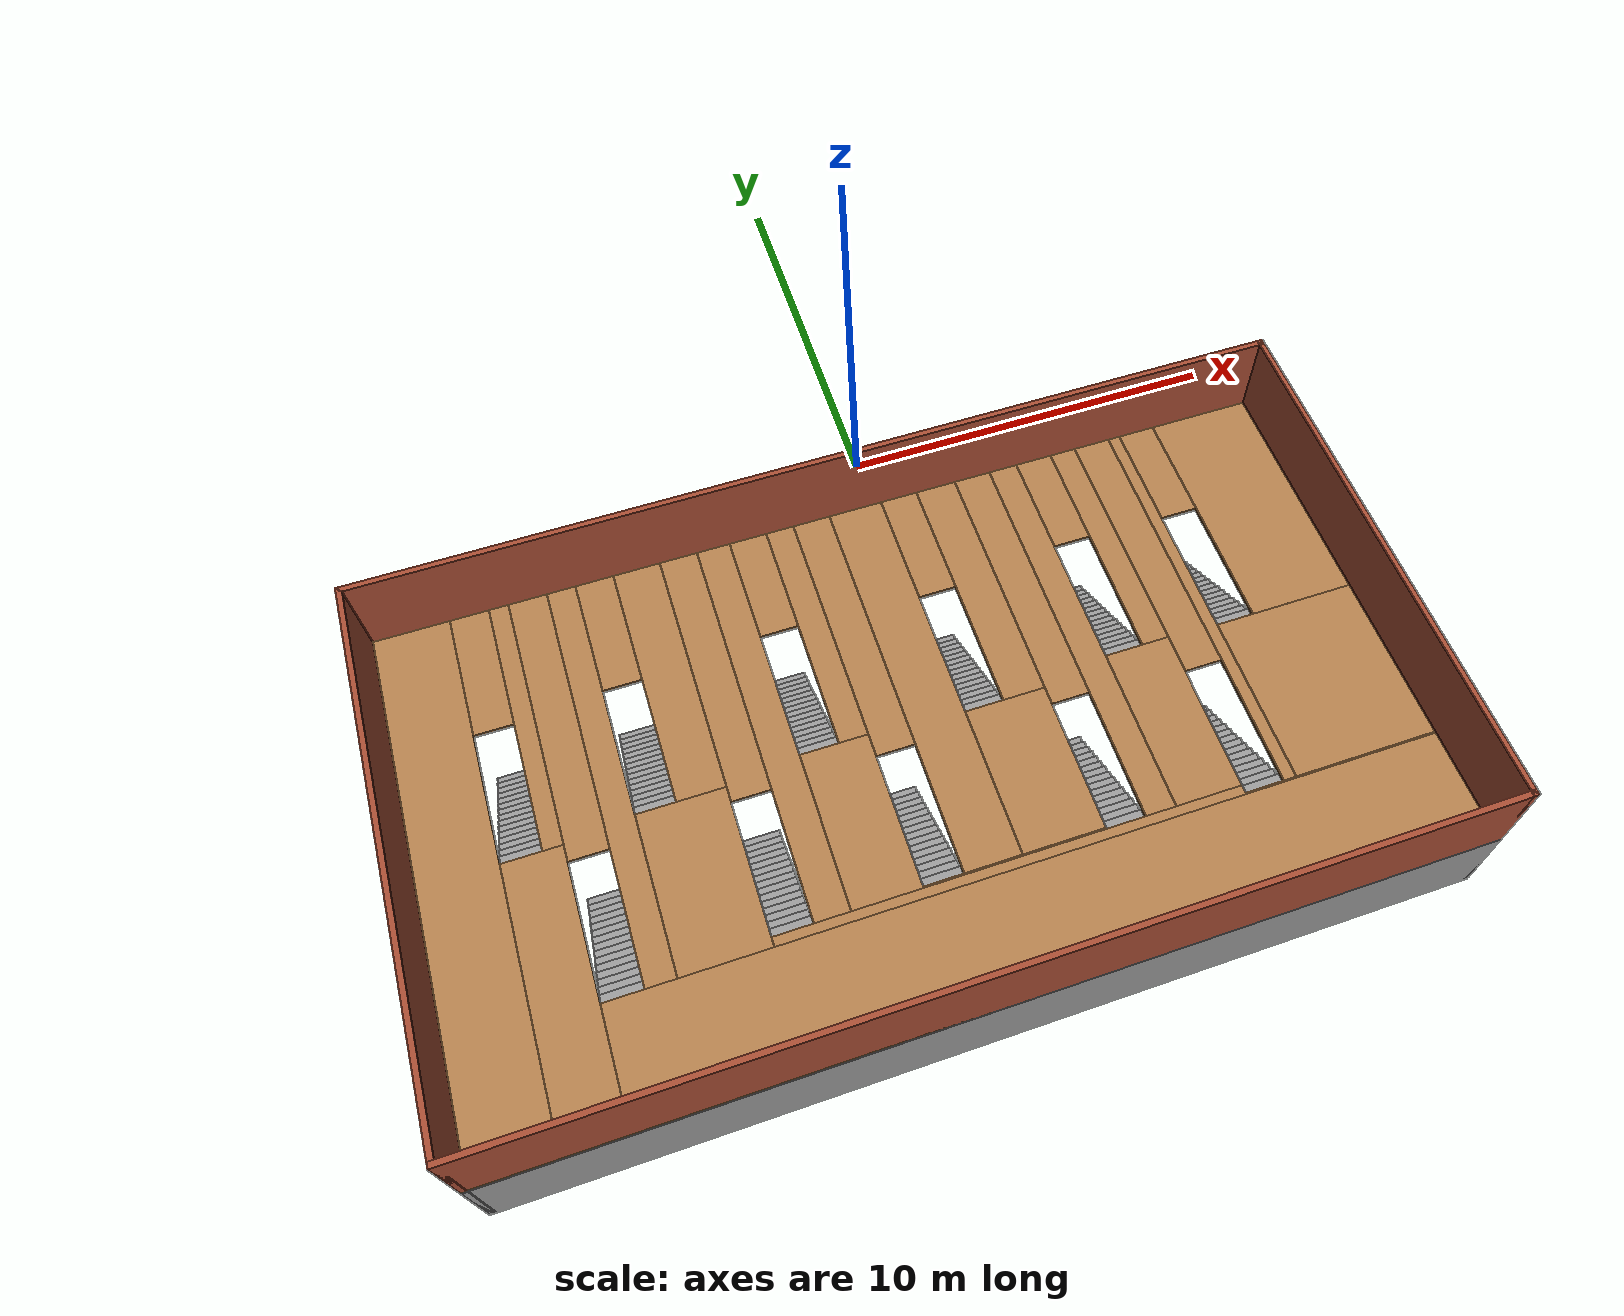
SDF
<sdf version="1.6">
 <world name="default">
  <light name="sun" type="directional">
   <pose>0 0 10 0 -0 0</pose>
   <diffuse>0.8 0.8 0.8 1</diffuse>
   <specular>0.2 0.2 0.2 1</specular>
   <attenuation>
    <range>1000</range>
    <constant>0.9</constant>
    <linear>0.01</linear>
    <quadratic>0.001</quadratic>
   </attenuation>
   <direction>-0.5 0.1 -0.9</direction>
  </light>
  <gravity>0 0 -9.8</gravity>
  <magnetic_field>6e-06 2.3e-05 -4.2e-05</magnetic_field>
  <atmosphere type="adiabatic"/>
  <physics name="default_physics" default="0" type="ode">
   <max_step_size>0.001</max_step_size>
   <real_time_factor>1</real_time_factor>
   <real_time_update_rate>1000</real_time_update_rate>
  </physics>
  <scene><ambient>0.4 0.4 0.4 1</ambient><background>0.7 0.7 0.7 1</background><shadows>1</shadows></scene>
  <audio><device>default</device></audio>
  <spherical_coordinates>
   <surface_model>EARTH_WGS84</surface_model>
   <latitude_deg>0</latitude_deg>
   <longitude_deg>0</longitude_deg>
   <elevation>0</elevation>
   <heading_deg>0</heading_deg>
  </spherical_coordinates>
  <model name="Untitled_2">
   <pose>-1.18521 -8.18185 -2.6 0 -0 0</pose>
   <link name="Floor_4">
    <pose>1e-06 0 2.5 0 -0 0</pose>
    <visual name="Floor_4_Visual_0">
     <pose>-11.2032 0 0.05 0 -0 0</pose>
     <geometry><box><size>2.09357 14 0.1</size></box></geometry>
     <material>
      <script><uri>file://media/materials/scripts/gazebo.material</uri><name>Gazebo/Wood</name></script>
      <ambient>1 1 1 1</ambient>
     </material>
     <meta><layer>1</layer></meta>
    </visual>
    <collision name="Floor_4_Collision_0">
     <geometry><box><size>2.09357 14 0.1</size></box></geometry>
     <pose>-11.2032 0 0.05 0 -0 0</pose>
    </collision>
    <visual name="Floor_4_Visual_1">
     <pose>-9.40436 -3.55244 0.05 0 -0 0</pose>
     <geometry><box><size>1.50415 6.89513 0.1</size></box></geometry>
     <material>
      <script><uri>file://media/materials/scripts/gazebo.material</uri><name>Gazebo/Wood</name></script>
      <ambient>1 1 1 1</ambient>
     </material>
     <meta><layer>1</layer></meta>
    </visual>
    <collision name="Floor_4_Collision_1">
     <geometry><box><size>1.50415 6.89513 0.1</size></box></geometry>
     <pose>-9.40436 -3.55244 0.05 0 -0 0</pose>
    </collision>
    <visual name="Floor_4_Visual_2">
     <pose>1.79886 -5.52881 0.05 0 -0 0</pose>
     <geometry><box><size>20.9023 2.94238 0.1</size></box></geometry>
     <material>
      <script><uri>file://media/materials/scripts/gazebo.material</uri><name>Gazebo/Wood</name></script>
      <ambient>1 1 1 1</ambient>
     </material>
     <meta><layer>1</layer></meta>
    </visual>
    <collision name="Floor_4_Collision_2">
     <geometry><box><size>20.9023 2.94238 0.1</size></box></geometry>
     <pose>1.79886 -5.52881 0.05 0 -0 0</pose>
    </collision>
    <visual name="Floor_4_Visual_3">
     <pose>-7.27778 1.47119 0.05 0 -0 0</pose>
     <geometry><box><size>0.749006 11.0576 0.1</size></box></geometry>
     <material>
      <script><uri>file://media/materials/scripts/gazebo.material</uri><name>Gazebo/Wood</name></script>
      <ambient>1 1 1 1</ambient>
     </material>
     <meta><layer>1</layer></meta>
    </visual>
    <collision name="Floor_4_Collision_3">
     <geometry><box><size>0.749006 11.0576 0.1</size></box></geometry>
     <pose>-7.27778 1.47119 0.05 0 -0 0</pose>
    </collision>
    <visual name="Floor_4_Visual_4">
     <pose>-5.78392 -1.97631 0.05 0 -0 0</pose>
     <geometry><box><size>2.23873 4.16263 0.1</size></box></geometry>
     <material>
      <script><uri>file://media/materials/scripts/gazebo.material</uri><name>Gazebo/Wood</name></script>
      <ambient>1 1 1 1</ambient>
     </material>
     <meta><layer>1</layer></meta>
    </visual>
    <collision name="Floor_4_Collision_4">
     <geometry><box><size>2.23873 4.16263 0.1</size></box></geometry>
     <pose>-5.78392 -1.97631 0.05 0 -0 0</pose>
    </collision>
    <visual name="Floor_4_Visual_5">
     <pose>1.17713 -3.93519 0.05 0 -0 0</pose>
     <geometry><box><size>11.6834 0.244861 0.1</size></box></geometry>
     <material>
      <script><uri>file://media/materials/scripts/gazebo.material</uri><name>Gazebo/Wood</name></script>
      <ambient>1 1 1 1</ambient>
     </material>
     <meta><layer>1</layer></meta>
    </visual>
    <collision name="Floor_4_Collision_5">
     <geometry><box><size>11.6834 0.244861 0.1</size></box></geometry>
     <pose>1.17713 -3.93519 0.05 0 -0 0</pose>
    </collision>
    <visual name="Floor_4_Visual_6">
     <pose>9.6344 -4.04013 0.05 0 -0 0</pose>
     <geometry><box><size>5.23119 0.03498 0.1</size></box></geometry>
     <material>
      <script><uri>file://media/materials/scripts/gazebo.material</uri><name>Gazebo/Wood</name></script>
      <ambient>1 1 1 1</ambient>
     </material>
     <meta><layer>1</layer></meta>
    </visual>
    <collision name="Floor_4_Collision_6">
     <geometry><box><size>5.23119 0.03498 0.1</size></box></geometry>
     <pose>9.6344 -4.04013 0.05 0 -0 0</pose>
    </collision>
    <visual name="Floor_4_Visual_7">
     <pose>8.18343 1.48868 0.05 0 -0 0</pose>
     <geometry><box><size>0.329245 11.0226 0.1</size></box></geometry>
     <material>
      <script><uri>file://media/materials/scripts/gazebo.material</uri><name>Gazebo/Wood</name></script>
      <ambient>1 1 1 1</ambient>
     </material>
     <meta><layer>1</layer></meta>
    </visual>
    <collision name="Floor_4_Collision_7">
     <geometry><box><size>0.329245 11.0226 0.1</size></box></geometry>
     <pose>8.18343 1.48868 0.05 0 -0 0</pose>
    </collision>
    <visual name="Floor_4_Visual_8">
     <pose>10.299 -1.78392 0.05 0 -0 0</pose>
     <geometry><box><size>3.90194 4.47746 0.1</size></box></geometry>
     <material>
      <script><uri>file://media/materials/scripts/gazebo.material</uri><name>Gazebo/Wood</name></script>
      <ambient>1 1 1 1</ambient>
     </material>
     <meta><layer>1</layer></meta>
    </visual>
    <collision name="Floor_4_Collision_8">
     <geometry><box><size>3.90194 4.47746 0.1</size></box></geometry>
     <pose>10.299 -1.78392 0.05 0 -0 0</pose>
    </collision>
    <visual name="Floor_4_Visual_9">
     <pose>-3.22009 1.59362 0.05 0 -0 0</pose>
     <geometry><box><size>0.888927 10.8128 0.1</size></box></geometry>
     <material>
      <script><uri>file://media/materials/scripts/gazebo.material</uri><name>Gazebo/Wood</name></script>
      <ambient>1 1 1 1</ambient>
     </material>
     <meta><layer>1</layer></meta>
    </visual>
    <collision name="Floor_4_Collision_9">
     <geometry><box><size>0.888927 10.8128 0.1</size></box></geometry>
     <pose>-3.22009 1.59362 0.05 0 -0 0</pose>
    </collision>
    <visual name="Floor_4_Visual_10">
     <pose>4.91279 1.59362 0.05 0 -0 0</pose>
     <geometry><box><size>0.783986 10.8128 0.1</size></box></geometry>
     <material>
      <script><uri>file://media/materials/scripts/gazebo.material</uri><name>Gazebo/Wood</name></script>
      <ambient>1 1 1 1</ambient>
     </material>
     <meta><layer>1</layer></meta>
    </visual>
    <collision name="Floor_4_Collision_10">
     <geometry><box><size>0.783986 10.8128 0.1</size></box></geometry>
     <pose>4.91279 1.59362 0.05 0 -0 0</pose>
    </collision>
    <visual name="Floor_4_Visual_11">
     <pose>-1.90112 -1.73145 0.05 0 -0 0</pose>
     <geometry><box><size>1.74901 4.16263 0.1</size></box></geometry>
     <material>
      <script><uri>file://media/materials/scripts/gazebo.material</uri><name>Gazebo/Wood</name></script>
      <ambient>1 1 1 1</ambient>
     </material>
     <meta><layer>1</layer></meta>
    </visual>
    <collision name="Floor_4_Collision_11">
     <geometry><box><size>1.74901 4.16263 0.1</size></box></geometry>
     <pose>-1.90112 -1.73145 0.05 0 -0 0</pose>
    </collision>
    <visual name="Floor_4_Visual_12">
     <pose>6.1618 -1.644 0.05 0 -0 0</pose>
     <geometry><box><size>1.71403 4.33754 0.1</size></box></geometry>
     <material>
      <script><uri>file://media/materials/scripts/gazebo.material</uri><name>Gazebo/Wood</name></script>
      <ambient>1 1 1 1</ambient>
     </material>
     <meta><layer>1</layer></meta>
    </visual>
    <collision name="Floor_4_Collision_12">
     <geometry><box><size>1.71403 4.33754 0.1</size></box></geometry>
     <pose>6.1618 -1.644 0.05 0 -0 0</pose>
    </collision>
    <visual name="Floor_4_Visual_13">
     <pose>1.24709 -3.79527 0.05 0 -0 0</pose>
     <geometry><box><size>4.54742 0.034981 0.1</size></box></geometry>
     <material>
      <script><uri>file://media/materials/scripts/gazebo.material</uri><name>Gazebo/Wood</name></script>
      <ambient>1 1 1 1</ambient>
     </material>
     <meta><layer>1</layer></meta>
    </visual>
    <collision name="Floor_4_Collision_13">
     <geometry><box><size>4.54742 0.034981 0.1</size></box></geometry>
     <pose>1.24709 -3.79527 0.05 0 -0 0</pose>
    </collision>
    <visual name="Floor_4_Visual_14">
     <pose>0.697686 1.61111 0.05 0 -0 0</pose>
     <geometry><box><size>1.44861 10.7778 0.1</size></box></geometry>
     <material>
      <script><uri>file://media/materials/scripts/gazebo.material</uri><name>Gazebo/Wood</name></script>
      <ambient>1 1 1 1</ambient>
     </material>
     <meta><layer>1</layer></meta>
    </visual>
    <collision name="Floor_4_Collision_14">
     <geometry><box><size>1.44861 10.7778 0.1</size></box></geometry>
     <pose>0.697686 1.61111 0.05 0 -0 0</pose>
    </collision>
    <visual name="Floor_4_Visual_15">
     <pose>2.47139 -1.80141 0.05 0 -0 0</pose>
     <geometry><box><size>2.09881 3.95275 0.1</size></box></geometry>
     <material>
      <script><uri>file://media/materials/scripts/gazebo.material</uri><name>Gazebo/Wood</name></script>
      <ambient>1 1 1 1</ambient>
     </material>
     <meta><layer>1</layer></meta>
    </visual>
    <collision name="Floor_4_Collision_15">
     <geometry><box><size>2.09881 3.95275 0.1</size></box></geometry>
     <pose>2.47139 -1.80141 0.05 0 -0 0</pose>
    </collision>
    <visual name="Floor_4_Visual_16">
     <pose>-8.15228 3.22119 0.05 0 -0 0</pose>
     <geometry><box><size>1 7.55762 0.1</size></box></geometry>
     <material>
      <script><uri>file://media/materials/scripts/gazebo.material</uri><name>Gazebo/Wood</name></script>
      <ambient>1 1 1 1</ambient>
     </material>
     <meta><layer>1</layer></meta>
    </visual>
    <collision name="Floor_4_Collision_16">
     <geometry><box><size>1 7.55762 0.1</size></box></geometry>
     <pose>-8.15228 3.22119 0.05 0 -0 0</pose>
    </collision>
    <visual name="Floor_4_Visual_17">
     <pose>7.51881 3.23868 0.05 0 -0 0</pose>
     <geometry><box><size>1 7.52264 0.1</size></box></geometry>
     <material>
      <script><uri>file://media/materials/scripts/gazebo.material</uri><name>Gazebo/Wood</name></script>
      <ambient>1 1 1 1</ambient>
     </material>
     <meta><layer>1</layer></meta>
    </visual>
    <collision name="Floor_4_Collision_17">
     <geometry><box><size>1 7.52264 0.1</size></box></geometry>
     <pose>7.51881 3.23868 0.05 0 -0 0</pose>
    </collision>
    <visual name="Floor_4_Visual_18">
     <pose>-4.16455 3.34362 0.05 0 -0 0</pose>
     <geometry><box><size>1 7.31276 0.1</size></box></geometry>
     <material>
      <script><uri>file://media/materials/scripts/gazebo.material</uri><name>Gazebo/Wood</name></script>
      <ambient>1 1 1 1</ambient>
     </material>
     <meta><layer>1</layer></meta>
    </visual>
    <collision name="Floor_4_Collision_18">
     <geometry><box><size>1 7.31276 0.1</size></box></geometry>
     <pose>-4.16455 3.34362 0.05 0 -0 0</pose>
    </collision>
    <visual name="Floor_4_Visual_19">
     <pose>4.0208 3.34362 0.05 0 -0 0</pose>
     <geometry><box><size>1 7.31276 0.1</size></box></geometry>
     <material>
      <script><uri>file://media/materials/scripts/gazebo.material</uri><name>Gazebo/Wood</name></script>
      <ambient>1 1 1 1</ambient>
     </material>
     <meta><layer>1</layer></meta>
    </visual>
    <collision name="Floor_4_Collision_19">
     <geometry><box><size>1 7.31276 0.1</size></box></geometry>
     <pose>4.0208 3.34362 0.05 0 -0 0</pose>
    </collision>
    <visual name="Floor_4_Visual_20">
     <pose>-0.526618 3.36111 0.05 0 -0 0</pose>
     <geometry><box><size>1 7.27778 0.1</size></box></geometry>
     <material>
      <script><uri>file://media/materials/scripts/gazebo.material</uri><name>Gazebo/Wood</name></script>
      <ambient>1 1 1 1</ambient>
     </material>
     <meta><layer>1</layer></meta>
    </visual>
    <collision name="Floor_4_Collision_20">
     <geometry><box><size>1 7.27778 0.1</size></box></geometry>
     <pose>-0.526618 3.36111 0.05 0 -0 0</pose>
    </collision>
    <visual name="Floor_4_Visual_21">
     <pose>-8.90436 3.44756 0.05 0 -0 0</pose>
     <geometry><box><size>0.504146 7.10487 0.1</size></box></geometry>
     <material>
      <script><uri>file://media/materials/scripts/gazebo.material</uri><name>Gazebo/Wood</name></script>
      <ambient>1 1 1 1</ambient>
     </material>
     <meta><layer>1</layer></meta>
    </visual>
    <collision name="Floor_4_Collision_21">
     <geometry><box><size>0.504146 7.10487 0.1</size></box></geometry>
     <pose>-8.90436 3.44756 0.05 0 -0 0</pose>
    </collision>
    <visual name="Floor_4_Visual_22">
     <pose>-5.28392 3.55251 0.05 0 -0 0</pose>
     <geometry><box><size>1.23873 6.89499 0.1</size></box></geometry>
     <material>
      <script><uri>file://media/materials/scripts/gazebo.material</uri><name>Gazebo/Wood</name></script>
      <ambient>1 1 1 1</ambient>
     </material>
     <meta><layer>1</layer></meta>
    </visual>
    <collision name="Floor_4_Collision_22">
     <geometry><box><size>1.23873 6.89499 0.1</size></box></geometry>
     <pose>-5.28392 3.55251 0.05 0 -0 0</pose>
    </collision>
    <visual name="Floor_4_Visual_23">
     <pose>2.97139 3.58749 0.05 0 -0 0</pose>
     <geometry><box><size>1.09881 6.82503 0.1</size></box></geometry>
     <material>
      <script><uri>file://media/materials/scripts/gazebo.material</uri><name>Gazebo/Wood</name></script>
      <ambient>1 1 1 1</ambient>
     </material>
     <meta><layer>1</layer></meta>
    </visual>
    <collision name="Floor_4_Collision_23">
     <geometry><box><size>1.09881 6.82503 0.1</size></box></geometry>
     <pose>2.97139 3.58749 0.05 0 -0 0</pose>
    </collision>
    <visual name="Floor_4_Visual_24">
     <pose>-1.40112 3.67494 0.05 0 -0 0</pose>
     <geometry><box><size>0.749006 6.65013 0.1</size></box></geometry>
     <material>
      <script><uri>file://media/materials/scripts/gazebo.material</uri><name>Gazebo/Wood</name></script>
      <ambient>1 1 1 1</ambient>
     </material>
     <meta><layer>1</layer></meta>
    </visual>
    <collision name="Floor_4_Collision_24">
     <geometry><box><size>0.749006 6.65013 0.1</size></box></geometry>
     <pose>-1.40112 3.67494 0.05 0 -0 0</pose>
    </collision>
    <visual name="Floor_4_Visual_25">
     <pose>10.799 3.72741 0.05 0 -0 0</pose>
     <geometry><box><size>2.90194 6.54519 0.1</size></box></geometry>
     <material>
      <script><uri>file://media/materials/scripts/gazebo.material</uri><name>Gazebo/Wood</name></script>
      <ambient>1 1 1 1</ambient>
     </material>
     <meta><layer>1</layer></meta>
    </visual>
    <collision name="Floor_4_Collision_25">
     <geometry><box><size>2.90194 6.54519 0.1</size></box></geometry>
     <pose>10.799 3.72741 0.05 0 -0 0</pose>
    </collision>
    <visual name="Floor_4_Visual_26">
     <pose>6.6618 3.76239 0.05 0 -0 0</pose>
     <geometry><box><size>0.714026 6.47523 0.1</size></box></geometry>
     <material>
      <script><uri>file://media/materials/scripts/gazebo.material</uri><name>Gazebo/Wood</name></script>
      <ambient>1 1 1 1</ambient>
     </material>
     <meta><layer>1</layer></meta>
    </visual>
    <collision name="Floor_4_Collision_26">
     <geometry><box><size>0.714026 6.47523 0.1</size></box></geometry>
     <pose>6.6618 3.76239 0.05 0 -0 0</pose>
    </collision>
    <visual name="Floor_4_Visual_27">
     <pose>-9.65643 5.19756 0.05 0 -0 0</pose>
     <geometry><box><size>1 3.60487 0.1</size></box></geometry>
     <material>
      <script><uri>file://media/materials/scripts/gazebo.material</uri><name>Gazebo/Wood</name></script>
      <ambient>1 1 1 1</ambient>
     </material>
     <meta><layer>1</layer></meta>
    </visual>
    <collision name="Floor_4_Collision_27">
     <geometry><box><size>1 3.60487 0.1</size></box></geometry>
     <pose>-9.65643 5.19756 0.05 0 -0 0</pose>
    </collision>
    <visual name="Floor_4_Visual_28">
     <pose>-6.40328 5.30251 0.05 0 -0 0</pose>
     <geometry><box><size>1 3.39499 0.1</size></box></geometry>
     <material>
      <script><uri>file://media/materials/scripts/gazebo.material</uri><name>Gazebo/Wood</name></script>
      <ambient>1 1 1 1</ambient>
     </material>
     <meta><layer>1</layer></meta>
    </visual>
    <collision name="Floor_4_Collision_28">
     <geometry><box><size>1 3.39499 0.1</size></box></geometry>
     <pose>-6.40328 5.30251 0.05 0 -0 0</pose>
    </collision>
    <visual name="Floor_4_Visual_29">
     <pose>1.92199 5.33749 0.05 0 -0 0</pose>
     <geometry><box><size>1 3.32503 0.1</size></box></geometry>
     <material>
      <script><uri>file://media/materials/scripts/gazebo.material</uri><name>Gazebo/Wood</name></script>
      <ambient>1 1 1 1</ambient>
     </material>
     <meta><layer>1</layer></meta>
    </visual>
    <collision name="Floor_4_Collision_29">
     <geometry><box><size>1 3.32503 0.1</size></box></geometry>
     <pose>1.92199 5.33749 0.05 0 -0 0</pose>
    </collision>
    <visual name="Floor_4_Visual_30">
     <pose>-2.27562 5.42494 0.05 0 -0 0</pose>
     <geometry><box><size>1 3.15013 0.1</size></box></geometry>
     <material>
      <script><uri>file://media/materials/scripts/gazebo.material</uri><name>Gazebo/Wood</name></script>
      <ambient>1 1 1 1</ambient>
     </material>
     <meta><layer>1</layer></meta>
    </visual>
    <collision name="Floor_4_Collision_30">
     <geometry><box><size>1 3.15013 0.1</size></box></geometry>
     <pose>-2.27562 5.42494 0.05 0 -0 0</pose>
    </collision>
    <visual name="Floor_4_Visual_31">
     <pose>8.84806 5.47741 0.05 0 -0 0</pose>
     <geometry><box><size>1 3.04519 0.1</size></box></geometry>
     <material>
      <script><uri>file://media/materials/scripts/gazebo.material</uri><name>Gazebo/Wood</name></script>
      <ambient>1 1 1 1</ambient>
     </material>
     <meta><layer>1</layer></meta>
    </visual>
    <collision name="Floor_4_Collision_31">
     <geometry><box><size>1 3.04519 0.1</size></box></geometry>
     <pose>8.84806 5.47741 0.05 0 -0 0</pose>
    </collision>
    <visual name="Floor_4_Visual_32">
     <pose>5.80478 5.51239 0.05 0 -0 0</pose>
     <geometry><box><size>1 2.97523 0.1</size></box></geometry>
     <material>
      <script><uri>file://media/materials/scripts/gazebo.material</uri><name>Gazebo/Wood</name></script>
      <ambient>1 1 1 1</ambient>
     </material>
     <meta><layer>1</layer></meta>
    </visual>
    <collision name="Floor_4_Collision_32">
     <geometry><box><size>1 2.97523 0.1</size></box></geometry>
     <pose>5.80478 5.51239 0.05 0 -0 0</pose>
    </collision>
   </link>
   <link name="Stairs_37">
    <visual name="Stairs_37_Visual_0">
     <pose>-9.65643 3.27846 0.083333 0 -0 0</pose>
     <geometry><box><size>1 0.233333 0.166667</size></box></geometry>
     <material>
      <script><uri>file://media/materials/scripts/gazebo.material</uri><name>Gazebo/Grey</name></script>
      <ambient>1 1 1 1</ambient>
     </material>
     <meta><layer>0</layer></meta>
    </visual>
    <collision name="Stairs_37_Collision_0">
     <geometry><box><size>1 0.233333 0.166667</size></box></geometry>
     <pose>-9.65643 3.27846 0.083333 0 -0 0</pose>
    </collision>
    <visual name="Stairs_37_Visual_1">
     <pose>-9.65643 3.04513 0.25 0 -0 0</pose>
     <geometry><box><size>1 0.233333 0.166667</size></box></geometry>
     <material>
      <script><uri>file://media/materials/scripts/gazebo.material</uri><name>Gazebo/Grey</name></script>
      <ambient>1 1 1 1</ambient>
     </material>
     <meta><layer>0</layer></meta>
    </visual>
    <collision name="Stairs_37_Collision_1">
     <geometry><box><size>1 0.233333 0.166667</size></box></geometry>
     <pose>-9.65643 3.04513 0.25 0 -0 0</pose>
    </collision>
    <visual name="Stairs_37_Visual_2">
     <pose>-9.65643 2.8118 0.416667 0 -0 0</pose>
     <geometry><box><size>1 0.233333 0.166667</size></box></geometry>
     <material>
      <script><uri>file://media/materials/scripts/gazebo.material</uri><name>Gazebo/Grey</name></script>
      <ambient>1 1 1 1</ambient>
     </material>
     <meta><layer>0</layer></meta>
    </visual>
    <collision name="Stairs_37_Collision_2">
     <geometry><box><size>1 0.233333 0.166667</size></box></geometry>
     <pose>-9.65643 2.8118 0.416667 0 -0 0</pose>
    </collision>
    <visual name="Stairs_37_Visual_3">
     <pose>-9.65643 2.57846 0.583333 0 -0 0</pose>
     <geometry><box><size>1 0.233333 0.166667</size></box></geometry>
     <material>
      <script><uri>file://media/materials/scripts/gazebo.material</uri><name>Gazebo/Grey</name></script>
      <ambient>1 1 1 1</ambient>
     </material>
     <meta><layer>0</layer></meta>
    </visual>
    <collision name="Stairs_37_Collision_3">
     <geometry><box><size>1 0.233333 0.166667</size></box></geometry>
     <pose>-9.65643 2.57846 0.583333 0 -0 0</pose>
    </collision>
    <visual name="Stairs_37_Visual_4">
     <pose>-9.65643 2.34513 0.75 0 -0 0</pose>
     <geometry><box><size>1 0.233333 0.166667</size></box></geometry>
     <material>
      <script><uri>file://media/materials/scripts/gazebo.material</uri><name>Gazebo/Grey</name></script>
      <ambient>1 1 1 1</ambient>
     </material>
     <meta><layer>0</layer></meta>
    </visual>
    <collision name="Stairs_37_Collision_4">
     <geometry><box><size>1 0.233333 0.166667</size></box></geometry>
     <pose>-9.65643 2.34513 0.75 0 -0 0</pose>
    </collision>
    <visual name="Stairs_37_Visual_5">
     <pose>-9.65643 2.1118 0.916667 0 -0 0</pose>
     <geometry><box><size>1 0.233333 0.166667</size></box></geometry>
     <material>
      <script><uri>file://media/materials/scripts/gazebo.material</uri><name>Gazebo/Grey</name></script>
      <ambient>1 1 1 1</ambient>
     </material>
     <meta><layer>0</layer></meta>
    </visual>
    <collision name="Stairs_37_Collision_5">
     <geometry><box><size>1 0.233333 0.166667</size></box></geometry>
     <pose>-9.65643 2.1118 0.916667 0 -0 0</pose>
    </collision>
    <visual name="Stairs_37_Visual_6">
     <pose>-9.65643 1.87846 1.08333 0 -0 0</pose>
     <geometry><box><size>1 0.233333 0.166667</size></box></geometry>
     <material>
      <script><uri>file://media/materials/scripts/gazebo.material</uri><name>Gazebo/Grey</name></script>
      <ambient>1 1 1 1</ambient>
     </material>
     <meta><layer>0</layer></meta>
    </visual>
    <collision name="Stairs_37_Collision_6">
     <geometry><box><size>1 0.233333 0.166667</size></box></geometry>
     <pose>-9.65643 1.87846 1.08333 0 -0 0</pose>
    </collision>
    <visual name="Stairs_37_Visual_7">
     <pose>-9.65643 1.64513 1.25 0 -0 0</pose>
     <geometry><box><size>1 0.233333 0.166667</size></box></geometry>
     <material>
      <script><uri>file://media/materials/scripts/gazebo.material</uri><name>Gazebo/Grey</name></script>
      <ambient>1 1 1 1</ambient>
     </material>
     <meta><layer>0</layer></meta>
    </visual>
    <collision name="Stairs_37_Collision_7">
     <geometry><box><size>1 0.233333 0.166667</size></box></geometry>
     <pose>-9.65643 1.64513 1.25 0 -0 0</pose>
    </collision>
    <visual name="Stairs_37_Visual_8">
     <pose>-9.65643 1.4118 1.41667 0 -0 0</pose>
     <geometry><box><size>1 0.233333 0.166667</size></box></geometry>
     <material>
      <script><uri>file://media/materials/scripts/gazebo.material</uri><name>Gazebo/Grey</name></script>
      <ambient>1 1 1 1</ambient>
     </material>
     <meta><layer>0</layer></meta>
    </visual>
    <collision name="Stairs_37_Collision_8">
     <geometry><box><size>1 0.233333 0.166667</size></box></geometry>
     <pose>-9.65643 1.4118 1.41667 0 -0 0</pose>
    </collision>
    <visual name="Stairs_37_Visual_9">
     <pose>-9.65643 1.17846 1.58333 0 -0 0</pose>
     <geometry><box><size>1 0.233333 0.166667</size></box></geometry>
     <material>
      <script><uri>file://media/materials/scripts/gazebo.material</uri><name>Gazebo/Grey</name></script>
      <ambient>1 1 1 1</ambient>
     </material>
     <meta><layer>0</layer></meta>
    </visual>
    <collision name="Stairs_37_Collision_9">
     <geometry><box><size>1 0.233333 0.166667</size></box></geometry>
     <pose>-9.65643 1.17846 1.58333 0 -0 0</pose>
    </collision>
    <visual name="Stairs_37_Visual_10">
     <pose>-9.65643 0.94513 1.75 0 -0 0</pose>
     <geometry><box><size>1 0.233333 0.166667</size></box></geometry>
     <material>
      <script><uri>file://media/materials/scripts/gazebo.material</uri><name>Gazebo/Grey</name></script>
      <ambient>1 1 1 1</ambient>
     </material>
     <meta><layer>0</layer></meta>
    </visual>
    <collision name="Stairs_37_Collision_10">
     <geometry><box><size>1 0.233333 0.166667</size></box></geometry>
     <pose>-9.65643 0.94513 1.75 0 -0 0</pose>
    </collision>
    <visual name="Stairs_37_Visual_11">
     <pose>-9.65643 0.711797 1.91667 0 -0 0</pose>
     <geometry><box><size>1 0.233333 0.166667</size></box></geometry>
     <material>
      <script><uri>file://media/materials/scripts/gazebo.material</uri><name>Gazebo/Grey</name></script>
      <ambient>1 1 1 1</ambient>
     </material>
     <meta><layer>0</layer></meta>
    </visual>
    <collision name="Stairs_37_Collision_11">
     <geometry><box><size>1 0.233333 0.166667</size></box></geometry>
     <pose>-9.65643 0.711797 1.91667 0 -0 0</pose>
    </collision>
    <visual name="Stairs_37_Visual_12">
     <pose>-9.65643 0.478463 2.08333 0 -0 0</pose>
     <geometry><box><size>1 0.233333 0.166667</size></box></geometry>
     <material>
      <script><uri>file://media/materials/scripts/gazebo.material</uri><name>Gazebo/Grey</name></script>
      <ambient>1 1 1 1</ambient>
     </material>
     <meta><layer>0</layer></meta>
    </visual>
    <collision name="Stairs_37_Collision_12">
     <geometry><box><size>1 0.233333 0.166667</size></box></geometry>
     <pose>-9.65643 0.478463 2.08333 0 -0 0</pose>
    </collision>
    <visual name="Stairs_37_Visual_13">
     <pose>-9.65643 0.24513 2.25 0 -0 0</pose>
     <geometry><box><size>1 0.233333 0.166667</size></box></geometry>
     <material>
      <script><uri>file://media/materials/scripts/gazebo.material</uri><name>Gazebo/Grey</name></script>
      <ambient>1 1 1 1</ambient>
     </material>
     <meta><layer>0</layer></meta>
    </visual>
    <collision name="Stairs_37_Collision_13">
     <geometry><box><size>1 0.233333 0.166667</size></box></geometry>
     <pose>-9.65643 0.24513 2.25 0 -0 0</pose>
    </collision>
    <visual name="Stairs_37_Visual_14">
     <pose>-9.65643 0.011797 2.41667 0 -0 0</pose>
     <geometry><box><size>1 0.233333 0.166667</size></box></geometry>
     <material>
      <script><uri>file://media/materials/scripts/gazebo.material</uri><name>Gazebo/Grey</name></script>
      <ambient>1 1 1 1</ambient>
     </material>
     <meta><layer>0</layer></meta>
    </visual>
    <collision name="Stairs_37_Collision_14">
     <geometry><box><size>1 0.233333 0.166667</size></box></geometry>
     <pose>-9.65643 0.011797 2.41667 0 -0 0</pose>
    </collision>
   </link>
   <link name="Stairs_38">
    <visual name="Stairs_38_Visual_0">
     <pose>-8.15228 -0.674291 0.083333 0 -0 0</pose>
     <geometry><box><size>1 0.233333 0.166667</size></box></geometry>
     <material>
      <script><uri>file://media/materials/scripts/gazebo.material</uri><name>Gazebo/Grey</name></script>
      <ambient>1 1 1 1</ambient>
     </material>
     <meta><layer>0</layer></meta>
    </visual>
    <collision name="Stairs_38_Collision_0">
     <geometry><box><size>1 0.233333 0.166667</size></box></geometry>
     <pose>-8.15228 -0.674291 0.083333 0 -0 0</pose>
    </collision>
    <visual name="Stairs_38_Visual_1">
     <pose>-8.15228 -0.907624 0.25 0 -0 0</pose>
     <geometry><box><size>1 0.233333 0.166667</size></box></geometry>
     <material>
      <script><uri>file://media/materials/scripts/gazebo.material</uri><name>Gazebo/Grey</name></script>
      <ambient>1 1 1 1</ambient>
     </material>
     <meta><layer>0</layer></meta>
    </visual>
    <collision name="Stairs_38_Collision_1">
     <geometry><box><size>1 0.233333 0.166667</size></box></geometry>
     <pose>-8.15228 -0.907624 0.25 0 -0 0</pose>
    </collision>
    <visual name="Stairs_38_Visual_2">
     <pose>-8.15228 -1.14096 0.416667 0 -0 0</pose>
     <geometry><box><size>1 0.233333 0.166667</size></box></geometry>
     <material>
      <script><uri>file://media/materials/scripts/gazebo.material</uri><name>Gazebo/Grey</name></script>
      <ambient>1 1 1 1</ambient>
     </material>
     <meta><layer>0</layer></meta>
    </visual>
    <collision name="Stairs_38_Collision_2">
     <geometry><box><size>1 0.233333 0.166667</size></box></geometry>
     <pose>-8.15228 -1.14096 0.416667 0 -0 0</pose>
    </collision>
    <visual name="Stairs_38_Visual_3">
     <pose>-8.15228 -1.37429 0.583333 0 -0 0</pose>
     <geometry><box><size>1 0.233333 0.166667</size></box></geometry>
     <material>
      <script><uri>file://media/materials/scripts/gazebo.material</uri><name>Gazebo/Grey</name></script>
      <ambient>1 1 1 1</ambient>
     </material>
     <meta><layer>0</layer></meta>
    </visual>
    <collision name="Stairs_38_Collision_3">
     <geometry><box><size>1 0.233333 0.166667</size></box></geometry>
     <pose>-8.15228 -1.37429 0.583333 0 -0 0</pose>
    </collision>
    <visual name="Stairs_38_Visual_4">
     <pose>-8.15228 -1.60762 0.75 0 -0 0</pose>
     <geometry><box><size>1 0.233333 0.166667</size></box></geometry>
     <material>
      <script><uri>file://media/materials/scripts/gazebo.material</uri><name>Gazebo/Grey</name></script>
      <ambient>1 1 1 1</ambient>
     </material>
     <meta><layer>0</layer></meta>
    </visual>
    <collision name="Stairs_38_Collision_4">
     <geometry><box><size>1 0.233333 0.166667</size></box></geometry>
     <pose>-8.15228 -1.60762 0.75 0 -0 0</pose>
    </collision>
    <visual name="Stairs_38_Visual_5">
     <pose>-8.15228 -1.84096 0.916667 0 -0 0</pose>
     <geometry><box><size>1 0.233333 0.166667</size></box></geometry>
     <material>
      <script><uri>file://media/materials/scripts/gazebo.material</uri><name>Gazebo/Grey</name></script>
      <ambient>1 1 1 1</ambient>
     </material>
     <meta><layer>0</layer></meta>
    </visual>
    <collision name="Stairs_38_Collision_5">
     <geometry><box><size>1 0.233333 0.166667</size></box></geometry>
     <pose>-8.15228 -1.84096 0.916667 0 -0 0</pose>
    </collision>
    <visual name="Stairs_38_Visual_6">
     <pose>-8.15228 -2.07429 1.08333 0 -0 0</pose>
     <geometry><box><size>1 0.233333 0.166667</size></box></geometry>
     <material>
      <script><uri>file://media/materials/scripts/gazebo.material</uri><name>Gazebo/Grey</name></script>
      <ambient>1 1 1 1</ambient>
     </material>
     <meta><layer>0</layer></meta>
    </visual>
    <collision name="Stairs_38_Collision_6">
     <geometry><box><size>1 0.233333 0.166667</size></box></geometry>
     <pose>-8.15228 -2.07429 1.08333 0 -0 0</pose>
    </collision>
    <visual name="Stairs_38_Visual_7">
     <pose>-8.15228 -2.30762 1.25 0 -0 0</pose>
     <geometry><box><size>1 0.233333 0.166667</size></box></geometry>
     <material>
      <script><uri>file://media/materials/scripts/gazebo.material</uri><name>Gazebo/Grey</name></script>
      <ambient>1 1 1 1</ambient>
     </material>
     <meta><layer>0</layer></meta>
    </visual>
    <collision name="Stairs_38_Collision_7">
     <geometry><box><size>1 0.233333 0.166667</size></box></geometry>
     <pose>-8.15228 -2.30762 1.25 0 -0 0</pose>
    </collision>
    <visual name="Stairs_38_Visual_8">
     <pose>-8.15228 -2.54096 1.41667 0 -0 0</pose>
     <geometry><box><size>1 0.233333 0.166667</size></box></geometry>
     <material>
      <script><uri>file://media/materials/scripts/gazebo.material</uri><name>Gazebo/Grey</name></script>
      <ambient>1 1 1 1</ambient>
     </material>
     <meta><layer>0</layer></meta>
    </visual>
    <collision name="Stairs_38_Collision_8">
     <geometry><box><size>1 0.233333 0.166667</size></box></geometry>
     <pose>-8.15228 -2.54096 1.41667 0 -0 0</pose>
    </collision>
    <visual name="Stairs_38_Visual_9">
     <pose>-8.15228 -2.77429 1.58333 0 -0 0</pose>
     <geometry><box><size>1 0.233333 0.166667</size></box></geometry>
     <material>
      <script><uri>file://media/materials/scripts/gazebo.material</uri><name>Gazebo/Grey</name></script>
      <ambient>1 1 1 1</ambient>
     </material>
     <meta><layer>0</layer></meta>
    </visual>
    <collision name="Stairs_38_Collision_9">
     <geometry><box><size>1 0.233333 0.166667</size></box></geometry>
     <pose>-8.15228 -2.77429 1.58333 0 -0 0</pose>
    </collision>
    <visual name="Stairs_38_Visual_10">
     <pose>-8.15228 -3.00762 1.75 0 -0 0</pose>
     <geometry><box><size>1 0.233333 0.166667</size></box></geometry>
     <material>
      <script><uri>file://media/materials/scripts/gazebo.material</uri><name>Gazebo/Grey</name></script>
      <ambient>1 1 1 1</ambient>
     </material>
     <meta><layer>0</layer></meta>
    </visual>
    <collision name="Stairs_38_Collision_10">
     <geometry><box><size>1 0.233333 0.166667</size></box></geometry>
     <pose>-8.15228 -3.00762 1.75 0 -0 0</pose>
    </collision>
    <visual name="Stairs_38_Visual_11">
     <pose>-8.15228 -3.24096 1.91667 0 -0 0</pose>
     <geometry><box><size>1 0.233333 0.166667</size></box></geometry>
     <material>
      <script><uri>file://media/materials/scripts/gazebo.material</uri><name>Gazebo/Grey</name></script>
      <ambient>1 1 1 1</ambient>
     </material>
     <meta><layer>0</layer></meta>
    </visual>
    <collision name="Stairs_38_Collision_11">
     <geometry><box><size>1 0.233333 0.166667</size></box></geometry>
     <pose>-8.15228 -3.24096 1.91667 0 -0 0</pose>
    </collision>
    <visual name="Stairs_38_Visual_12">
     <pose>-8.15228 -3.47429 2.08333 0 -0 0</pose>
     <geometry><box><size>1 0.233333 0.166667</size></box></geometry>
     <material>
      <script><uri>file://media/materials/scripts/gazebo.material</uri><name>Gazebo/Grey</name></script>
      <ambient>1 1 1 1</ambient>
     </material>
     <meta><layer>0</layer></meta>
    </visual>
    <collision name="Stairs_38_Collision_12">
     <geometry><box><size>1 0.233333 0.166667</size></box></geometry>
     <pose>-8.15228 -3.47429 2.08333 0 -0 0</pose>
    </collision>
    <visual name="Stairs_38_Visual_13">
     <pose>-8.15228 -3.70762 2.25 0 -0 0</pose>
     <geometry><box><size>1 0.233333 0.166667</size></box></geometry>
     <material>
      <script><uri>file://media/materials/scripts/gazebo.material</uri><name>Gazebo/Grey</name></script>
      <ambient>1 1 1 1</ambient>
     </material>
     <meta><layer>0</layer></meta>
    </visual>
    <collision name="Stairs_38_Collision_13">
     <geometry><box><size>1 0.233333 0.166667</size></box></geometry>
     <pose>-8.15228 -3.70762 2.25 0 -0 0</pose>
    </collision>
    <visual name="Stairs_38_Visual_14">
     <pose>-8.15228 -3.94096 2.41667 0 -0 0</pose>
     <geometry><box><size>1 0.233333 0.166667</size></box></geometry>
     <material>
      <script><uri>file://media/materials/scripts/gazebo.material</uri><name>Gazebo/Grey</name></script>
      <ambient>1 1 1 1</ambient>
     </material>
     <meta><layer>0</layer></meta>
    </visual>
    <collision name="Stairs_38_Collision_14">
     <geometry><box><size>1 0.233333 0.166667</size></box></geometry>
     <pose>-8.15228 -3.94096 2.41667 0 -0 0</pose>
    </collision>
   </link>
   <link name="Stairs_39">
    <visual name="Stairs_39_Visual_0">
     <pose>-6.40328 3.48834 0.083333 0 -0 0</pose>
     <geometry><box><size>1 0.233333 0.166667</size></box></geometry>
     <material>
      <script><uri>file://media/materials/scripts/gazebo.material</uri><name>Gazebo/Grey</name></script>
      <ambient>1 1 1 1</ambient>
     </material>
     <meta><layer>0</layer></meta>
    </visual>
    <collision name="Stairs_39_Collision_0">
     <geometry><box><size>1 0.233333 0.166667</size></box></geometry>
     <pose>-6.40328 3.48834 0.083333 0 -0 0</pose>
    </collision>
    <visual name="Stairs_39_Visual_1">
     <pose>-6.40328 3.25501 0.25 0 -0 0</pose>
     <geometry><box><size>1 0.233333 0.166667</size></box></geometry>
     <material>
      <script><uri>file://media/materials/scripts/gazebo.material</uri><name>Gazebo/Grey</name></script>
      <ambient>1 1 1 1</ambient>
     </material>
     <meta><layer>0</layer></meta>
    </visual>
    <collision name="Stairs_39_Collision_1">
     <geometry><box><size>1 0.233333 0.166667</size></box></geometry>
     <pose>-6.40328 3.25501 0.25 0 -0 0</pose>
    </collision>
    <visual name="Stairs_39_Visual_2">
     <pose>-6.40328 3.02168 0.416667 0 -0 0</pose>
     <geometry><box><size>1 0.233333 0.166667</size></box></geometry>
     <material>
      <script><uri>file://media/materials/scripts/gazebo.material</uri><name>Gazebo/Grey</name></script>
      <ambient>1 1 1 1</ambient>
     </material>
     <meta><layer>0</layer></meta>
    </visual>
    <collision name="Stairs_39_Collision_2">
     <geometry><box><size>1 0.233333 0.166667</size></box></geometry>
     <pose>-6.40328 3.02168 0.416667 0 -0 0</pose>
    </collision>
    <visual name="Stairs_39_Visual_3">
     <pose>-6.40328 2.78834 0.583333 0 -0 0</pose>
     <geometry><box><size>1 0.233333 0.166667</size></box></geometry>
     <material>
      <script><uri>file://media/materials/scripts/gazebo.material</uri><name>Gazebo/Grey</name></script>
      <ambient>1 1 1 1</ambient>
     </material>
     <meta><layer>0</layer></meta>
    </visual>
    <collision name="Stairs_39_Collision_3">
     <geometry><box><size>1 0.233333 0.166667</size></box></geometry>
     <pose>-6.40328 2.78834 0.583333 0 -0 0</pose>
    </collision>
    <visual name="Stairs_39_Visual_4">
     <pose>-6.40328 2.55501 0.75 0 -0 0</pose>
     <geometry><box><size>1 0.233333 0.166667</size></box></geometry>
     <material>
      <script><uri>file://media/materials/scripts/gazebo.material</uri><name>Gazebo/Grey</name></script>
      <ambient>1 1 1 1</ambient>
     </material>
     <meta><layer>0</layer></meta>
    </visual>
    <collision name="Stairs_39_Collision_4">
     <geometry><box><size>1 0.233333 0.166667</size></box></geometry>
     <pose>-6.40328 2.55501 0.75 0 -0 0</pose>
    </collision>
    <visual name="Stairs_39_Visual_5">
     <pose>-6.40328 2.32168 0.916667 0 -0 0</pose>
     <geometry><box><size>1 0.233333 0.166667</size></box></geometry>
     <material>
      <script><uri>file://media/materials/scripts/gazebo.material</uri><name>Gazebo/Grey</name></script>
      <ambient>1 1 1 1</ambient>
     </material>
     <meta><layer>0</layer></meta>
    </visual>
    <collision name="Stairs_39_Collision_5">
     <geometry><box><size>1 0.233333 0.166667</size></box></geometry>
     <pose>-6.40328 2.32168 0.916667 0 -0 0</pose>
    </collision>
    <visual name="Stairs_39_Visual_6">
     <pose>-6.40328 2.08834 1.08333 0 -0 0</pose>
     <geometry><box><size>1 0.233333 0.166667</size></box></geometry>
     <material>
      <script><uri>file://media/materials/scripts/gazebo.material</uri><name>Gazebo/Grey</name></script>
      <ambient>1 1 1 1</ambient>
     </material>
     <meta><layer>0</layer></meta>
    </visual>
    <collision name="Stairs_39_Collision_6">
     <geometry><box><size>1 0.233333 0.166667</size></box></geometry>
     <pose>-6.40328 2.08834 1.08333 0 -0 0</pose>
    </collision>
    <visual name="Stairs_39_Visual_7">
     <pose>-6.40328 1.85501 1.25 0 -0 0</pose>
     <geometry><box><size>1 0.233333 0.166667</size></box></geometry>
     <material>
      <script><uri>file://media/materials/scripts/gazebo.material</uri><name>Gazebo/Grey</name></script>
      <ambient>1 1 1 1</ambient>
     </material>
     <meta><layer>0</layer></meta>
    </visual>
    <collision name="Stairs_39_Collision_7">
     <geometry><box><size>1 0.233333 0.166667</size></box></geometry>
     <pose>-6.40328 1.85501 1.25 0 -0 0</pose>
    </collision>
    <visual name="Stairs_39_Visual_8">
     <pose>-6.40328 1.62168 1.41667 0 -0 0</pose>
     <geometry><box><size>1 0.233333 0.166667</size></box></geometry>
     <material>
      <script><uri>file://media/materials/scripts/gazebo.material</uri><name>Gazebo/Grey</name></script>
      <ambient>1 1 1 1</ambient>
     </material>
     <meta><layer>0</layer></meta>
    </visual>
    <collision name="Stairs_39_Collision_8">
     <geometry><box><size>1 0.233333 0.166667</size></box></geometry>
     <pose>-6.40328 1.62168 1.41667 0 -0 0</pose>
    </collision>
    <visual name="Stairs_39_Visual_9">
     <pose>-6.40328 1.38834 1.58333 0 -0 0</pose>
     <geometry><box><size>1 0.233333 0.166667</size></box></geometry>
     <material>
      <script><uri>file://media/materials/scripts/gazebo.material</uri><name>Gazebo/Grey</name></script>
      <ambient>1 1 1 1</ambient>
     </material>
     <meta><layer>0</layer></meta>
    </visual>
    <collision name="Stairs_39_Collision_9">
     <geometry><box><size>1 0.233333 0.166667</size></box></geometry>
     <pose>-6.40328 1.38834 1.58333 0 -0 0</pose>
    </collision>
    <visual name="Stairs_39_Visual_10">
     <pose>-6.40328 1.15501 1.75 0 -0 0</pose>
     <geometry><box><size>1 0.233333 0.166667</size></box></geometry>
     <material>
      <script><uri>file://media/materials/scripts/gazebo.material</uri><name>Gazebo/Grey</name></script>
      <ambient>1 1 1 1</ambient>
     </material>
     <meta><layer>0</layer></meta>
    </visual>
    <collision name="Stairs_39_Collision_10">
     <geometry><box><size>1 0.233333 0.166667</size></box></geometry>
     <pose>-6.40328 1.15501 1.75 0 -0 0</pose>
    </collision>
    <visual name="Stairs_39_Visual_11">
     <pose>-6.40328 0.921678 1.91667 0 -0 0</pose>
     <geometry><box><size>1 0.233333 0.166667</size></box></geometry>
     <material>
      <script><uri>file://media/materials/scripts/gazebo.material</uri><name>Gazebo/Grey</name></script>
      <ambient>1 1 1 1</ambient>
     </material>
     <meta><layer>0</layer></meta>
    </visual>
    <collision name="Stairs_39_Collision_11">
     <geometry><box><size>1 0.233333 0.166667</size></box></geometry>
     <pose>-6.40328 0.921678 1.91667 0 -0 0</pose>
    </collision>
    <visual name="Stairs_39_Visual_12">
     <pose>-6.40328 0.688344 2.08333 0 -0 0</pose>
     <geometry><box><size>1 0.233333 0.166667</size></box></geometry>
     <material>
      <script><uri>file://media/materials/scripts/gazebo.material</uri><name>Gazebo/Grey</name></script>
      <ambient>1 1 1 1</ambient>
     </material>
     <meta><layer>0</layer></meta>
    </visual>
    <collision name="Stairs_39_Collision_12">
     <geometry><box><size>1 0.233333 0.166667</size></box></geometry>
     <pose>-6.40328 0.688344 2.08333 0 -0 0</pose>
    </collision>
    <visual name="Stairs_39_Visual_13">
     <pose>-6.40328 0.455011 2.25 0 -0 0</pose>
     <geometry><box><size>1 0.233333 0.166667</size></box></geometry>
     <material>
      <script><uri>file://media/materials/scripts/gazebo.material</uri><name>Gazebo/Grey</name></script>
      <ambient>1 1 1 1</ambient>
     </material>
     <meta><layer>0</layer></meta>
    </visual>
    <collision name="Stairs_39_Collision_13">
     <geometry><box><size>1 0.233333 0.166667</size></box></geometry>
     <pose>-6.40328 0.455011 2.25 0 -0 0</pose>
    </collision>
    <visual name="Stairs_39_Visual_14">
     <pose>-6.40328 0.221678 2.41667 0 -0 0</pose>
     <geometry><box><size>1 0.233333 0.166667</size></box></geometry>
     <material>
      <script><uri>file://media/materials/scripts/gazebo.material</uri><name>Gazebo/Grey</name></script>
      <ambient>1 1 1 1</ambient>
     </material>
     <meta><layer>0</layer></meta>
    </visual>
    <collision name="Stairs_39_Collision_14">
     <geometry><box><size>1 0.233333 0.166667</size></box></geometry>
     <pose>-6.40328 0.221678 2.41667 0 -0 0</pose>
    </collision>
   </link>
   <link name="Stairs_40">
    <visual name="Stairs_40_Visual_0">
     <pose>-4.16455 -0.42943 0.083333 0 -0 0</pose>
     <geometry><box><size>1 0.233333 0.166667</size></box></geometry>
     <material>
      <script><uri>file://media/materials/scripts/gazebo.material</uri><name>Gazebo/Grey</name></script>
      <ambient>1 1 1 1</ambient>
     </material>
     <meta><layer>0</layer></meta>
    </visual>
    <collision name="Stairs_40_Collision_0">
     <geometry><box><size>1 0.233333 0.166667</size></box></geometry>
     <pose>-4.16455 -0.42943 0.083333 0 -0 0</pose>
    </collision>
    <visual name="Stairs_40_Visual_1">
     <pose>-4.16455 -0.662764 0.25 0 -0 0</pose>
     <geometry><box><size>1 0.233333 0.166667</size></box></geometry>
     <material>
      <script><uri>file://media/materials/scripts/gazebo.material</uri><name>Gazebo/Grey</name></script>
      <ambient>1 1 1 1</ambient>
     </material>
     <meta><layer>0</layer></meta>
    </visual>
    <collision name="Stairs_40_Collision_1">
     <geometry><box><size>1 0.233333 0.166667</size></box></geometry>
     <pose>-4.16455 -0.662764 0.25 0 -0 0</pose>
    </collision>
    <visual name="Stairs_40_Visual_2">
     <pose>-4.16455 -0.896096 0.416667 0 -0 0</pose>
     <geometry><box><size>1 0.233333 0.166667</size></box></geometry>
     <material>
      <script><uri>file://media/materials/scripts/gazebo.material</uri><name>Gazebo/Grey</name></script>
      <ambient>1 1 1 1</ambient>
     </material>
     <meta><layer>0</layer></meta>
    </visual>
    <collision name="Stairs_40_Collision_2">
     <geometry><box><size>1 0.233333 0.166667</size></box></geometry>
     <pose>-4.16455 -0.896096 0.416667 0 -0 0</pose>
    </collision>
    <visual name="Stairs_40_Visual_3">
     <pose>-4.16455 -1.12943 0.583333 0 -0 0</pose>
     <geometry><box><size>1 0.233333 0.166667</size></box></geometry>
     <material>
      <script><uri>file://media/materials/scripts/gazebo.material</uri><name>Gazebo/Grey</name></script>
      <ambient>1 1 1 1</ambient>
     </material>
     <meta><layer>0</layer></meta>
    </visual>
    <collision name="Stairs_40_Collision_3">
     <geometry><box><size>1 0.233333 0.166667</size></box></geometry>
     <pose>-4.16455 -1.12943 0.583333 0 -0 0</pose>
    </collision>
    <visual name="Stairs_40_Visual_4">
     <pose>-4.16455 -1.36276 0.75 0 -0 0</pose>
     <geometry><box><size>1 0.233333 0.166667</size></box></geometry>
     <material>
      <script><uri>file://media/materials/scripts/gazebo.material</uri><name>Gazebo/Grey</name></script>
      <ambient>1 1 1 1</ambient>
     </material>
     <meta><layer>0</layer></meta>
    </visual>
    <collision name="Stairs_40_Collision_4">
     <geometry><box><size>1 0.233333 0.166667</size></box></geometry>
     <pose>-4.16455 -1.36276 0.75 0 -0 0</pose>
    </collision>
    <visual name="Stairs_40_Visual_5">
     <pose>-4.16455 -1.5961 0.916667 0 -0 0</pose>
     <geometry><box><size>1 0.233333 0.166667</size></box></geometry>
     <material>
      <script><uri>file://media/materials/scripts/gazebo.material</uri><name>Gazebo/Grey</name></script>
      <ambient>1 1 1 1</ambient>
     </material>
     <meta><layer>0</layer></meta>
    </visual>
    <collision name="Stairs_40_Collision_5">
     <geometry><box><size>1 0.233333 0.166667</size></box></geometry>
     <pose>-4.16455 -1.5961 0.916667 0 -0 0</pose>
    </collision>
    <visual name="Stairs_40_Visual_6">
     <pose>-4.16455 -1.82943 1.08333 0 -0 0</pose>
     <geometry><box><size>1 0.233333 0.166667</size></box></geometry>
     <material>
      <script><uri>file://media/materials/scripts/gazebo.material</uri><name>Gazebo/Grey</name></script>
      <ambient>1 1 1 1</ambient>
     </material>
     <meta><layer>0</layer></meta>
    </visual>
    <collision name="Stairs_40_Collision_6">
     <geometry><box><size>1 0.233333 0.166667</size></box></geometry>
     <pose>-4.16455 -1.82943 1.08333 0 -0 0</pose>
    </collision>
    <visual name="Stairs_40_Visual_7">
     <pose>-4.16455 -2.06276 1.25 0 -0 0</pose>
     <geometry><box><size>1 0.233333 0.166667</size></box></geometry>
     <material>
      <script><uri>file://media/materials/scripts/gazebo.material</uri><name>Gazebo/Grey</name></script>
      <ambient>1 1 1 1</ambient>
     </material>
     <meta><layer>0</layer></meta>
    </visual>
    <collision name="Stairs_40_Collision_7">
     <geometry><box><size>1 0.233333 0.166667</size></box></geometry>
     <pose>-4.16455 -2.06276 1.25 0 -0 0</pose>
    </collision>
    <visual name="Stairs_40_Visual_8">
     <pose>-4.16455 -2.2961 1.41667 0 -0 0</pose>
     <geometry><box><size>1 0.233333 0.166667</size></box></geometry>
     <material>
      <script><uri>file://media/materials/scripts/gazebo.material</uri><name>Gazebo/Grey</name></script>
      <ambient>1 1 1 1</ambient>
     </material>
     <meta><layer>0</layer></meta>
    </visual>
    <collision name="Stairs_40_Collision_8">
     <geometry><box><size>1 0.233333 0.166667</size></box></geometry>
     <pose>-4.16455 -2.2961 1.41667 0 -0 0</pose>
    </collision>
    <visual name="Stairs_40_Visual_9">
     <pose>-4.16455 -2.52943 1.58333 0 -0 0</pose>
     <geometry><box><size>1 0.233333 0.166667</size></box></geometry>
     <material>
      <script><uri>file://media/materials/scripts/gazebo.material</uri><name>Gazebo/Grey</name></script>
      <ambient>1 1 1 1</ambient>
     </material>
     <meta><layer>0</layer></meta>
    </visual>
    <collision name="Stairs_40_Collision_9">
     <geometry><box><size>1 0.233333 0.166667</size></box></geometry>
     <pose>-4.16455 -2.52943 1.58333 0 -0 0</pose>
    </collision>
    <visual name="Stairs_40_Visual_10">
     <pose>-4.16455 -2.76276 1.75 0 -0 0</pose>
     <geometry><box><size>1 0.233333 0.166667</size></box></geometry>
     <material>
      <script><uri>file://media/materials/scripts/gazebo.material</uri><name>Gazebo/Grey</name></script>
      <ambient>1 1 1 1</ambient>
     </material>
     <meta><layer>0</layer></meta>
    </visual>
    <collision name="Stairs_40_Collision_10">
     <geometry><box><size>1 0.233333 0.166667</size></box></geometry>
     <pose>-4.16455 -2.76276 1.75 0 -0 0</pose>
    </collision>
    <visual name="Stairs_40_Visual_11">
     <pose>-4.16455 -2.9961 1.91667 0 -0 0</pose>
     <geometry><box><size>1 0.233333 0.166667</size></box></geometry>
     <material>
      <script><uri>file://media/materials/scripts/gazebo.material</uri><name>Gazebo/Grey</name></script>
      <ambient>1 1 1 1</ambient>
     </material>
     <meta><layer>0</layer></meta>
    </visual>
    <collision name="Stairs_40_Collision_11">
     <geometry><box><size>1 0.233333 0.166667</size></box></geometry>
     <pose>-4.16455 -2.9961 1.91667 0 -0 0</pose>
    </collision>
    <visual name="Stairs_40_Visual_12">
     <pose>-4.16455 -3.22943 2.08333 0 -0 0</pose>
     <geometry><box><size>1 0.233333 0.166667</size></box></geometry>
     <material>
      <script><uri>file://media/materials/scripts/gazebo.material</uri><name>Gazebo/Grey</name></script>
      <ambient>1 1 1 1</ambient>
     </material>
     <meta><layer>0</layer></meta>
    </visual>
    <collision name="Stairs_40_Collision_12">
     <geometry><box><size>1 0.233333 0.166667</size></box></geometry>
     <pose>-4.16455 -3.22943 2.08333 0 -0 0</pose>
    </collision>
    <visual name="Stairs_40_Visual_13">
     <pose>-4.16455 -3.46276 2.25 0 -0 0</pose>
     <geometry><box><size>1 0.233333 0.166667</size></box></geometry>
     <material>
      <script><uri>file://media/materials/scripts/gazebo.material</uri><name>Gazebo/Grey</name></script>
      <ambient>1 1 1 1</ambient>
     </material>
     <meta><layer>0</layer></meta>
    </visual>
    <collision name="Stairs_40_Collision_13">
     <geometry><box><size>1 0.233333 0.166667</size></box></geometry>
     <pose>-4.16455 -3.46276 2.25 0 -0 0</pose>
    </collision>
    <visual name="Stairs_40_Visual_14">
     <pose>-4.16455 -3.6961 2.41667 0 -0 0</pose>
     <geometry><box><size>1 0.233333 0.166667</size></box></geometry>
     <material>
      <script><uri>file://media/materials/scripts/gazebo.material</uri><name>Gazebo/Grey</name></script>
      <ambient>1 1 1 1</ambient>
     </material>
     <meta><layer>0</layer></meta>
    </visual>
    <collision name="Stairs_40_Collision_14">
     <geometry><box><size>1 0.233333 0.166667</size></box></geometry>
     <pose>-4.16455 -3.6961 2.41667 0 -0 0</pose>
    </collision>
   </link>
   <link name="Stairs_41">
    <visual name="Stairs_41_Visual_0">
     <pose>-2.27562 3.7332 0.083333 0 -0 0</pose>
     <geometry><box><size>1 0.233333 0.166667</size></box></geometry>
     <material>
      <script><uri>file://media/materials/scripts/gazebo.material</uri><name>Gazebo/Grey</name></script>
      <ambient>1 1 1 1</ambient>
     </material>
     <meta><layer>0</layer></meta>
    </visual>
    <collision name="Stairs_41_Collision_0">
     <geometry><box><size>1 0.233333 0.166667</size></box></geometry>
     <pose>-2.27562 3.7332 0.083333 0 -0 0</pose>
    </collision>
    <visual name="Stairs_41_Visual_1">
     <pose>-2.27562 3.49987 0.25 0 -0 0</pose>
     <geometry><box><size>1 0.233333 0.166667</size></box></geometry>
     <material>
      <script><uri>file://media/materials/scripts/gazebo.material</uri><name>Gazebo/Grey</name></script>
      <ambient>1 1 1 1</ambient>
     </material>
     <meta><layer>0</layer></meta>
    </visual>
    <collision name="Stairs_41_Collision_1">
     <geometry><box><size>1 0.233333 0.166667</size></box></geometry>
     <pose>-2.27562 3.49987 0.25 0 -0 0</pose>
    </collision>
    <visual name="Stairs_41_Visual_2">
     <pose>-2.27562 3.26654 0.416667 0 -0 0</pose>
     <geometry><box><size>1 0.233333 0.166667</size></box></geometry>
     <material>
      <script><uri>file://media/materials/scripts/gazebo.material</uri><name>Gazebo/Grey</name></script>
      <ambient>1 1 1 1</ambient>
     </material>
     <meta><layer>0</layer></meta>
    </visual>
    <collision name="Stairs_41_Collision_2">
     <geometry><box><size>1 0.233333 0.166667</size></box></geometry>
     <pose>-2.27562 3.26654 0.416667 0 -0 0</pose>
    </collision>
    <visual name="Stairs_41_Visual_3">
     <pose>-2.27562 3.03321 0.583333 0 -0 0</pose>
     <geometry><box><size>1 0.233333 0.166667</size></box></geometry>
     <material>
      <script><uri>file://media/materials/scripts/gazebo.material</uri><name>Gazebo/Grey</name></script>
      <ambient>1 1 1 1</ambient>
     </material>
     <meta><layer>0</layer></meta>
    </visual>
    <collision name="Stairs_41_Collision_3">
     <geometry><box><size>1 0.233333 0.166667</size></box></geometry>
     <pose>-2.27562 3.03321 0.583333 0 -0 0</pose>
    </collision>
    <visual name="Stairs_41_Visual_4">
     <pose>-2.27562 2.79987 0.75 0 -0 0</pose>
     <geometry><box><size>1 0.233333 0.166667</size></box></geometry>
     <material>
      <script><uri>file://media/materials/scripts/gazebo.material</uri><name>Gazebo/Grey</name></script>
      <ambient>1 1 1 1</ambient>
     </material>
     <meta><layer>0</layer></meta>
    </visual>
    <collision name="Stairs_41_Collision_4">
     <geometry><box><size>1 0.233333 0.166667</size></box></geometry>
     <pose>-2.27562 2.79987 0.75 0 -0 0</pose>
    </collision>
    <visual name="Stairs_41_Visual_5">
     <pose>-2.27562 2.56654 0.916667 0 -0 0</pose>
     <geometry><box><size>1 0.233333 0.166667</size></box></geometry>
     <material>
      <script><uri>file://media/materials/scripts/gazebo.material</uri><name>Gazebo/Grey</name></script>
      <ambient>1 1 1 1</ambient>
     </material>
     <meta><layer>0</layer></meta>
    </visual>
    <collision name="Stairs_41_Collision_5">
     <geometry><box><size>1 0.233333 0.166667</size></box></geometry>
     <pose>-2.27562 2.56654 0.916667 0 -0 0</pose>
    </collision>
    <visual name="Stairs_41_Visual_6">
     <pose>-2.27562 2.3332 1.08333 0 -0 0</pose>
     <geometry><box><size>1 0.233333 0.166667</size></box></geometry>
     <material>
      <script><uri>file://media/materials/scripts/gazebo.material</uri><name>Gazebo/Grey</name></script>
      <ambient>1 1 1 1</ambient>
     </material>
     <meta><layer>0</layer></meta>
    </visual>
    <collision name="Stairs_41_Collision_6">
     <geometry><box><size>1 0.233333 0.166667</size></box></geometry>
     <pose>-2.27562 2.3332 1.08333 0 -0 0</pose>
    </collision>
    <visual name="Stairs_41_Visual_7">
     <pose>-2.27562 2.09987 1.25 0 -0 0</pose>
     <geometry><box><size>1 0.233333 0.166667</size></box></geometry>
     <material>
      <script><uri>file://media/materials/scripts/gazebo.material</uri><name>Gazebo/Grey</name></script>
      <ambient>1 1 1 1</ambient>
     </material>
     <meta><layer>0</layer></meta>
    </visual>
    <collision name="Stairs_41_Collision_7">
     <geometry><box><size>1 0.233333 0.166667</size></box></geometry>
     <pose>-2.27562 2.09987 1.25 0 -0 0</pose>
    </collision>
    <visual name="Stairs_41_Visual_8">
     <pose>-2.27562 1.86654 1.41667 0 -0 0</pose>
     <geometry><box><size>1 0.233333 0.166667</size></box></geometry>
     <material>
      <script><uri>file://media/materials/scripts/gazebo.material</uri><name>Gazebo/Grey</name></script>
      <ambient>1 1 1 1</ambient>
     </material>
     <meta><layer>0</layer></meta>
    </visual>
    <collision name="Stairs_41_Collision_8">
     <geometry><box><size>1 0.233333 0.166667</size></box></geometry>
     <pose>-2.27562 1.86654 1.41667 0 -0 0</pose>
    </collision>
    <visual name="Stairs_41_Visual_9">
     <pose>-2.27562 1.63321 1.58333 0 -0 0</pose>
     <geometry><box><size>1 0.233333 0.166667</size></box></geometry>
     <material>
      <script><uri>file://media/materials/scripts/gazebo.material</uri><name>Gazebo/Grey</name></script>
      <ambient>1 1 1 1</ambient>
     </material>
     <meta><layer>0</layer></meta>
    </visual>
    <collision name="Stairs_41_Collision_9">
     <geometry><box><size>1 0.233333 0.166667</size></box></geometry>
     <pose>-2.27562 1.63321 1.58333 0 -0 0</pose>
    </collision>
    <visual name="Stairs_41_Visual_10">
     <pose>-2.27562 1.39987 1.75 0 -0 0</pose>
     <geometry><box><size>1 0.233333 0.166667</size></box></geometry>
     <material>
      <script><uri>file://media/materials/scripts/gazebo.material</uri><name>Gazebo/Grey</name></script>
      <ambient>1 1 1 1</ambient>
     </material>
     <meta><layer>0</layer></meta>
    </visual>
    <collision name="Stairs_41_Collision_10">
     <geometry><box><size>1 0.233333 0.166667</size></box></geometry>
     <pose>-2.27562 1.39987 1.75 0 -0 0</pose>
    </collision>
    <visual name="Stairs_41_Visual_11">
     <pose>-2.27562 1.16654 1.91667 0 -0 0</pose>
     <geometry><box><size>1 0.233333 0.166667</size></box></geometry>
     <material>
      <script><uri>file://media/materials/scripts/gazebo.material</uri><name>Gazebo/Grey</name></script>
      <ambient>1 1 1 1</ambient>
     </material>
     <meta><layer>0</layer></meta>
    </visual>
    <collision name="Stairs_41_Collision_11">
     <geometry><box><size>1 0.233333 0.166667</size></box></geometry>
     <pose>-2.27562 1.16654 1.91667 0 -0 0</pose>
    </collision>
    <visual name="Stairs_41_Visual_12">
     <pose>-2.27562 0.933206 2.08333 0 -0 0</pose>
     <geometry><box><size>1 0.233333 0.166667</size></box></geometry>
     <material>
      <script><uri>file://media/materials/scripts/gazebo.material</uri><name>Gazebo/Grey</name></script>
      <ambient>1 1 1 1</ambient>
     </material>
     <meta><layer>0</layer></meta>
    </visual>
    <collision name="Stairs_41_Collision_12">
     <geometry><box><size>1 0.233333 0.166667</size></box></geometry>
     <pose>-2.27562 0.933206 2.08333 0 -0 0</pose>
    </collision>
    <visual name="Stairs_41_Visual_13">
     <pose>-2.27562 0.699872 2.25 0 -0 0</pose>
     <geometry><box><size>1 0.233333 0.166667</size></box></geometry>
     <material>
      <script><uri>file://media/materials/scripts/gazebo.material</uri><name>Gazebo/Grey</name></script>
      <ambient>1 1 1 1</ambient>
     </material>
     <meta><layer>0</layer></meta>
    </visual>
    <collision name="Stairs_41_Collision_13">
     <geometry><box><size>1 0.233333 0.166667</size></box></geometry>
     <pose>-2.27562 0.699872 2.25 0 -0 0</pose>
    </collision>
    <visual name="Stairs_41_Visual_14">
     <pose>-2.27562 0.466539 2.41667 0 -0 0</pose>
     <geometry><box><size>1 0.233333 0.166667</size></box></geometry>
     <material>
      <script><uri>file://media/materials/scripts/gazebo.material</uri><name>Gazebo/Grey</name></script>
      <ambient>1 1 1 1</ambient>
     </material>
     <meta><layer>0</layer></meta>
    </visual>
    <collision name="Stairs_41_Collision_14">
     <geometry><box><size>1 0.233333 0.166667</size></box></geometry>
     <pose>-2.27562 0.466539 2.41667 0 -0 0</pose>
    </collision>
   </link>
   <link name="Stairs_42">
    <visual name="Stairs_42_Visual_0">
     <pose>-0.526618 -0.394449 0.083333 0 -0 0</pose>
     <geometry><box><size>1 0.233333 0.166667</size></box></geometry>
     <material>
      <script><uri>file://media/materials/scripts/gazebo.material</uri><name>Gazebo/Grey</name></script>
      <ambient>1 1 1 1</ambient>
     </material>
     <meta><layer>0</layer></meta>
    </visual>
    <collision name="Stairs_42_Collision_0">
     <geometry><box><size>1 0.233333 0.166667</size></box></geometry>
     <pose>-0.526618 -0.394449 0.083333 0 -0 0</pose>
    </collision>
    <visual name="Stairs_42_Visual_1">
     <pose>-0.526618 -0.627783 0.25 0 -0 0</pose>
     <geometry><box><size>1 0.233333 0.166667</size></box></geometry>
     <material>
      <script><uri>file://media/materials/scripts/gazebo.material</uri><name>Gazebo/Grey</name></script>
      <ambient>1 1 1 1</ambient>
     </material>
     <meta><layer>0</layer></meta>
    </visual>
    <collision name="Stairs_42_Collision_1">
     <geometry><box><size>1 0.233333 0.166667</size></box></geometry>
     <pose>-0.526618 -0.627783 0.25 0 -0 0</pose>
    </collision>
    <visual name="Stairs_42_Visual_2">
     <pose>-0.526618 -0.861115 0.416667 0 -0 0</pose>
     <geometry><box><size>1 0.233333 0.166667</size></box></geometry>
     <material>
      <script><uri>file://media/materials/scripts/gazebo.material</uri><name>Gazebo/Grey</name></script>
      <ambient>1 1 1 1</ambient>
     </material>
     <meta><layer>0</layer></meta>
    </visual>
    <collision name="Stairs_42_Collision_2">
     <geometry><box><size>1 0.233333 0.166667</size></box></geometry>
     <pose>-0.526618 -0.861115 0.416667 0 -0 0</pose>
    </collision>
    <visual name="Stairs_42_Visual_3">
     <pose>-0.526618 -1.09445 0.583333 0 -0 0</pose>
     <geometry><box><size>1 0.233333 0.166667</size></box></geometry>
     <material>
      <script><uri>file://media/materials/scripts/gazebo.material</uri><name>Gazebo/Grey</name></script>
      <ambient>1 1 1 1</ambient>
     </material>
     <meta><layer>0</layer></meta>
    </visual>
    <collision name="Stairs_42_Collision_3">
     <geometry><box><size>1 0.233333 0.166667</size></box></geometry>
     <pose>-0.526618 -1.09445 0.583333 0 -0 0</pose>
    </collision>
    <visual name="Stairs_42_Visual_4">
     <pose>-0.526618 -1.32778 0.75 0 -0 0</pose>
     <geometry><box><size>1 0.233333 0.166667</size></box></geometry>
     <material>
      <script><uri>file://media/materials/scripts/gazebo.material</uri><name>Gazebo/Grey</name></script>
      <ambient>1 1 1 1</ambient>
     </material>
     <meta><layer>0</layer></meta>
    </visual>
    <collision name="Stairs_42_Collision_4">
     <geometry><box><size>1 0.233333 0.166667</size></box></geometry>
     <pose>-0.526618 -1.32778 0.75 0 -0 0</pose>
    </collision>
    <visual name="Stairs_42_Visual_5">
     <pose>-0.526618 -1.56112 0.916667 0 -0 0</pose>
     <geometry><box><size>1 0.233333 0.166667</size></box></geometry>
     <material>
      <script><uri>file://media/materials/scripts/gazebo.material</uri><name>Gazebo/Grey</name></script>
      <ambient>1 1 1 1</ambient>
     </material>
     <meta><layer>0</layer></meta>
    </visual>
    <collision name="Stairs_42_Collision_5">
     <geometry><box><size>1 0.233333 0.166667</size></box></geometry>
     <pose>-0.526618 -1.56112 0.916667 0 -0 0</pose>
    </collision>
    <visual name="Stairs_42_Visual_6">
     <pose>-0.526618 -1.79445 1.08333 0 -0 0</pose>
     <geometry><box><size>1 0.233333 0.166667</size></box></geometry>
     <material>
      <script><uri>file://media/materials/scripts/gazebo.material</uri><name>Gazebo/Grey</name></script>
      <ambient>1 1 1 1</ambient>
     </material>
     <meta><layer>0</layer></meta>
    </visual>
    <collision name="Stairs_42_Collision_6">
     <geometry><box><size>1 0.233333 0.166667</size></box></geometry>
     <pose>-0.526618 -1.79445 1.08333 0 -0 0</pose>
    </collision>
    <visual name="Stairs_42_Visual_7">
     <pose>-0.526618 -2.02778 1.25 0 -0 0</pose>
     <geometry><box><size>1 0.233333 0.166667</size></box></geometry>
     <material>
      <script><uri>file://media/materials/scripts/gazebo.material</uri><name>Gazebo/Grey</name></script>
      <ambient>1 1 1 1</ambient>
     </material>
     <meta><layer>0</layer></meta>
    </visual>
    <collision name="Stairs_42_Collision_7">
     <geometry><box><size>1 0.233333 0.166667</size></box></geometry>
     <pose>-0.526618 -2.02778 1.25 0 -0 0</pose>
    </collision>
    <visual name="Stairs_42_Visual_8">
     <pose>-0.526618 -2.26112 1.41667 0 -0 0</pose>
     <geometry><box><size>1 0.233333 0.166667</size></box></geometry>
     <material>
      <script><uri>file://media/materials/scripts/gazebo.material</uri><name>Gazebo/Grey</name></script>
      <ambient>1 1 1 1</ambient>
     </material>
     <meta><layer>0</layer></meta>
    </visual>
    <collision name="Stairs_42_Collision_8">
     <geometry><box><size>1 0.233333 0.166667</size></box></geometry>
     <pose>-0.526618 -2.26112 1.41667 0 -0 0</pose>
    </collision>
    <visual name="Stairs_42_Visual_9">
     <pose>-0.526618 -2.49445 1.58333 0 -0 0</pose>
     <geometry><box><size>1 0.233333 0.166667</size></box></geometry>
     <material>
      <script><uri>file://media/materials/scripts/gazebo.material</uri><name>Gazebo/Grey</name></script>
      <ambient>1 1 1 1</ambient>
     </material>
     <meta><layer>0</layer></meta>
    </visual>
    <collision name="Stairs_42_Collision_9">
     <geometry><box><size>1 0.233333 0.166667</size></box></geometry>
     <pose>-0.526618 -2.49445 1.58333 0 -0 0</pose>
    </collision>
    <visual name="Stairs_42_Visual_10">
     <pose>-0.526618 -2.72778 1.75 0 -0 0</pose>
     <geometry><box><size>1 0.233333 0.166667</size></box></geometry>
     <material>
      <script><uri>file://media/materials/scripts/gazebo.material</uri><name>Gazebo/Grey</name></script>
      <ambient>1 1 1 1</ambient>
     </material>
     <meta><layer>0</layer></meta>
    </visual>
    <collision name="Stairs_42_Collision_10">
     <geometry><box><size>1 0.233333 0.166667</size></box></geometry>
     <pose>-0.526618 -2.72778 1.75 0 -0 0</pose>
    </collision>
    <visual name="Stairs_42_Visual_11">
     <pose>-0.526618 -2.96112 1.91667 0 -0 0</pose>
     <geometry><box><size>1 0.233333 0.166667</size></box></geometry>
     <material>
      <script><uri>file://media/materials/scripts/gazebo.material</uri><name>Gazebo/Grey</name></script>
      <ambient>1 1 1 1</ambient>
     </material>
     <meta><layer>0</layer></meta>
    </visual>
    <collision name="Stairs_42_Collision_11">
     <geometry><box><size>1 0.233333 0.166667</size></box></geometry>
     <pose>-0.526618 -2.96112 1.91667 0 -0 0</pose>
    </collision>
    <visual name="Stairs_42_Visual_12">
     <pose>-0.526618 -3.19445 2.08333 0 -0 0</pose>
     <geometry><box><size>1 0.233333 0.166667</size></box></geometry>
     <material>
      <script><uri>file://media/materials/scripts/gazebo.material</uri><name>Gazebo/Grey</name></script>
      <ambient>1 1 1 1</ambient>
     </material>
     <meta><layer>0</layer></meta>
    </visual>
    <collision name="Stairs_42_Collision_12">
     <geometry><box><size>1 0.233333 0.166667</size></box></geometry>
     <pose>-0.526618 -3.19445 2.08333 0 -0 0</pose>
    </collision>
    <visual name="Stairs_42_Visual_13">
     <pose>-0.526618 -3.42778 2.25 0 -0 0</pose>
     <geometry><box><size>1 0.233333 0.166667</size></box></geometry>
     <material>
      <script><uri>file://media/materials/scripts/gazebo.material</uri><name>Gazebo/Grey</name></script>
      <ambient>1 1 1 1</ambient>
     </material>
     <meta><layer>0</layer></meta>
    </visual>
    <collision name="Stairs_42_Collision_13">
     <geometry><box><size>1 0.233333 0.166667</size></box></geometry>
     <pose>-0.526618 -3.42778 2.25 0 -0 0</pose>
    </collision>
    <visual name="Stairs_42_Visual_14">
     <pose>-0.526618 -3.66112 2.41667 0 -0 0</pose>
     <geometry><box><size>1 0.233333 0.166667</size></box></geometry>
     <material>
      <script><uri>file://media/materials/scripts/gazebo.material</uri><name>Gazebo/Grey</name></script>
      <ambient>1 1 1 1</ambient>
     </material>
     <meta><layer>0</layer></meta>
    </visual>
    <collision name="Stairs_42_Collision_14">
     <geometry><box><size>1 0.233333 0.166667</size></box></geometry>
     <pose>-0.526618 -3.66112 2.41667 0 -0 0</pose>
    </collision>
   </link>
   <link name="Stairs_43">
    <visual name="Stairs_43_Visual_0">
     <pose>1.92199 3.5583 0.083333 0 -0 0</pose>
     <geometry><box><size>1 0.233333 0.166667</size></box></geometry>
     <material>
      <script><uri>file://media/materials/scripts/gazebo.material</uri><name>Gazebo/Grey</name></script>
      <ambient>1 1 1 1</ambient>
     </material>
     <meta><layer>0</layer></meta>
    </visual>
    <collision name="Stairs_43_Collision_0">
     <geometry><box><size>1 0.233333 0.166667</size></box></geometry>
     <pose>1.92199 3.5583 0.083333 0 -0 0</pose>
    </collision>
    <visual name="Stairs_43_Visual_1">
     <pose>1.92199 3.32497 0.25 0 -0 0</pose>
     <geometry><box><size>1 0.233333 0.166667</size></box></geometry>
     <material>
      <script><uri>file://media/materials/scripts/gazebo.material</uri><name>Gazebo/Grey</name></script>
      <ambient>1 1 1 1</ambient>
     </material>
     <meta><layer>0</layer></meta>
    </visual>
    <collision name="Stairs_43_Collision_1">
     <geometry><box><size>1 0.233333 0.166667</size></box></geometry>
     <pose>1.92199 3.32497 0.25 0 -0 0</pose>
    </collision>
    <visual name="Stairs_43_Visual_2">
     <pose>1.92199 3.09164 0.416667 0 -0 0</pose>
     <geometry><box><size>1 0.233333 0.166667</size></box></geometry>
     <material>
      <script><uri>file://media/materials/scripts/gazebo.material</uri><name>Gazebo/Grey</name></script>
      <ambient>1 1 1 1</ambient>
     </material>
     <meta><layer>0</layer></meta>
    </visual>
    <collision name="Stairs_43_Collision_2">
     <geometry><box><size>1 0.233333 0.166667</size></box></geometry>
     <pose>1.92199 3.09164 0.416667 0 -0 0</pose>
    </collision>
    <visual name="Stairs_43_Visual_3">
     <pose>1.92199 2.85831 0.583333 0 -0 0</pose>
     <geometry><box><size>1 0.233333 0.166667</size></box></geometry>
     <material>
      <script><uri>file://media/materials/scripts/gazebo.material</uri><name>Gazebo/Grey</name></script>
      <ambient>1 1 1 1</ambient>
     </material>
     <meta><layer>0</layer></meta>
    </visual>
    <collision name="Stairs_43_Collision_3">
     <geometry><box><size>1 0.233333 0.166667</size></box></geometry>
     <pose>1.92199 2.85831 0.583333 0 -0 0</pose>
    </collision>
    <visual name="Stairs_43_Visual_4">
     <pose>1.92199 2.62497 0.75 0 -0 0</pose>
     <geometry><box><size>1 0.233333 0.166667</size></box></geometry>
     <material>
      <script><uri>file://media/materials/scripts/gazebo.material</uri><name>Gazebo/Grey</name></script>
      <ambient>1 1 1 1</ambient>
     </material>
     <meta><layer>0</layer></meta>
    </visual>
    <collision name="Stairs_43_Collision_4">
     <geometry><box><size>1 0.233333 0.166667</size></box></geometry>
     <pose>1.92199 2.62497 0.75 0 -0 0</pose>
    </collision>
    <visual name="Stairs_43_Visual_5">
     <pose>1.92199 2.39164 0.916667 0 -0 0</pose>
     <geometry><box><size>1 0.233333 0.166667</size></box></geometry>
     <material>
      <script><uri>file://media/materials/scripts/gazebo.material</uri><name>Gazebo/Grey</name></script>
      <ambient>1 1 1 1</ambient>
     </material>
     <meta><layer>0</layer></meta>
    </visual>
    <collision name="Stairs_43_Collision_5">
     <geometry><box><size>1 0.233333 0.166667</size></box></geometry>
     <pose>1.92199 2.39164 0.916667 0 -0 0</pose>
    </collision>
    <visual name="Stairs_43_Visual_6">
     <pose>1.92199 2.1583 1.08333 0 -0 0</pose>
     <geometry><box><size>1 0.233333 0.166667</size></box></geometry>
     <material>
      <script><uri>file://media/materials/scripts/gazebo.material</uri><name>Gazebo/Grey</name></script>
      <ambient>1 1 1 1</ambient>
     </material>
     <meta><layer>0</layer></meta>
    </visual>
    <collision name="Stairs_43_Collision_6">
     <geometry><box><size>1 0.233333 0.166667</size></box></geometry>
     <pose>1.92199 2.1583 1.08333 0 -0 0</pose>
    </collision>
    <visual name="Stairs_43_Visual_7">
     <pose>1.92199 1.92497 1.25 0 -0 0</pose>
     <geometry><box><size>1 0.233333 0.166667</size></box></geometry>
     <material>
      <script><uri>file://media/materials/scripts/gazebo.material</uri><name>Gazebo/Grey</name></script>
      <ambient>1 1 1 1</ambient>
     </material>
     <meta><layer>0</layer></meta>
    </visual>
    <collision name="Stairs_43_Collision_7">
     <geometry><box><size>1 0.233333 0.166667</size></box></geometry>
     <pose>1.92199 1.92497 1.25 0 -0 0</pose>
    </collision>
    <visual name="Stairs_43_Visual_8">
     <pose>1.92199 1.69164 1.41667 0 -0 0</pose>
     <geometry><box><size>1 0.233333 0.166667</size></box></geometry>
     <material>
      <script><uri>file://media/materials/scripts/gazebo.material</uri><name>Gazebo/Grey</name></script>
      <ambient>1 1 1 1</ambient>
     </material>
     <meta><layer>0</layer></meta>
    </visual>
    <collision name="Stairs_43_Collision_8">
     <geometry><box><size>1 0.233333 0.166667</size></box></geometry>
     <pose>1.92199 1.69164 1.41667 0 -0 0</pose>
    </collision>
    <visual name="Stairs_43_Visual_9">
     <pose>1.92199 1.4583 1.58333 0 -0 0</pose>
     <geometry><box><size>1 0.233333 0.166667</size></box></geometry>
     <material>
      <script><uri>file://media/materials/scripts/gazebo.material</uri><name>Gazebo/Grey</name></script>
      <ambient>1 1 1 1</ambient>
     </material>
     <meta><layer>0</layer></meta>
    </visual>
    <collision name="Stairs_43_Collision_9">
     <geometry><box><size>1 0.233333 0.166667</size></box></geometry>
     <pose>1.92199 1.4583 1.58333 0 -0 0</pose>
    </collision>
    <visual name="Stairs_43_Visual_10">
     <pose>1.92199 1.22497 1.75 0 -0 0</pose>
     <geometry><box><size>1 0.233333 0.166667</size></box></geometry>
     <material>
      <script><uri>file://media/materials/scripts/gazebo.material</uri><name>Gazebo/Grey</name></script>
      <ambient>1 1 1 1</ambient>
     </material>
     <meta><layer>0</layer></meta>
    </visual>
    <collision name="Stairs_43_Collision_10">
     <geometry><box><size>1 0.233333 0.166667</size></box></geometry>
     <pose>1.92199 1.22497 1.75 0 -0 0</pose>
    </collision>
    <visual name="Stairs_43_Visual_11">
     <pose>1.92199 0.991638 1.91667 0 -0 0</pose>
     <geometry><box><size>1 0.233333 0.166667</size></box></geometry>
     <material>
      <script><uri>file://media/materials/scripts/gazebo.material</uri><name>Gazebo/Grey</name></script>
      <ambient>1 1 1 1</ambient>
     </material>
     <meta><layer>0</layer></meta>
    </visual>
    <collision name="Stairs_43_Collision_11">
     <geometry><box><size>1 0.233333 0.166667</size></box></geometry>
     <pose>1.92199 0.991638 1.91667 0 -0 0</pose>
    </collision>
    <visual name="Stairs_43_Visual_12">
     <pose>1.92199 0.758305 2.08333 0 -0 0</pose>
     <geometry><box><size>1 0.233333 0.166667</size></box></geometry>
     <material>
      <script><uri>file://media/materials/scripts/gazebo.material</uri><name>Gazebo/Grey</name></script>
      <ambient>1 1 1 1</ambient>
     </material>
     <meta><layer>0</layer></meta>
    </visual>
    <collision name="Stairs_43_Collision_12">
     <geometry><box><size>1 0.233333 0.166667</size></box></geometry>
     <pose>1.92199 0.758305 2.08333 0 -0 0</pose>
    </collision>
    <visual name="Stairs_43_Visual_13">
     <pose>1.92199 0.524971 2.25 0 -0 0</pose>
     <geometry><box><size>1 0.233333 0.166667</size></box></geometry>
     <material>
      <script><uri>file://media/materials/scripts/gazebo.material</uri><name>Gazebo/Grey</name></script>
      <ambient>1 1 1 1</ambient>
     </material>
     <meta><layer>0</layer></meta>
    </visual>
    <collision name="Stairs_43_Collision_13">
     <geometry><box><size>1 0.233333 0.166667</size></box></geometry>
     <pose>1.92199 0.524971 2.25 0 -0 0</pose>
    </collision>
    <visual name="Stairs_43_Visual_14">
     <pose>1.92199 0.291638 2.41667 0 -0 0</pose>
     <geometry><box><size>1 0.233333 0.166667</size></box></geometry>
     <material>
      <script><uri>file://media/materials/scripts/gazebo.material</uri><name>Gazebo/Grey</name></script>
      <ambient>1 1 1 1</ambient>
     </material>
     <meta><layer>0</layer></meta>
    </visual>
    <collision name="Stairs_43_Collision_14">
     <geometry><box><size>1 0.233333 0.166667</size></box></geometry>
     <pose>1.92199 0.291638 2.41667 0 -0 0</pose>
    </collision>
   </link>
   <link name="Stairs_44">
    <visual name="Stairs_44_Visual_0">
     <pose>4.0208 -0.42943 0.083333 0 -0 0</pose>
     <geometry><box><size>1 0.233333 0.166667</size></box></geometry>
     <material>
      <script><uri>file://media/materials/scripts/gazebo.material</uri><name>Gazebo/Grey</name></script>
      <ambient>1 1 1 1</ambient>
     </material>
     <meta><layer>0</layer></meta>
    </visual>
    <collision name="Stairs_44_Collision_0">
     <geometry><box><size>1 0.233333 0.166667</size></box></geometry>
     <pose>4.0208 -0.42943 0.083333 0 -0 0</pose>
    </collision>
    <visual name="Stairs_44_Visual_1">
     <pose>4.0208 -0.662764 0.25 0 -0 0</pose>
     <geometry><box><size>1 0.233333 0.166667</size></box></geometry>
     <material>
      <script><uri>file://media/materials/scripts/gazebo.material</uri><name>Gazebo/Grey</name></script>
      <ambient>1 1 1 1</ambient>
     </material>
     <meta><layer>0</layer></meta>
    </visual>
    <collision name="Stairs_44_Collision_1">
     <geometry><box><size>1 0.233333 0.166667</size></box></geometry>
     <pose>4.0208 -0.662764 0.25 0 -0 0</pose>
    </collision>
    <visual name="Stairs_44_Visual_2">
     <pose>4.0208 -0.896096 0.416667 0 -0 0</pose>
     <geometry><box><size>1 0.233333 0.166667</size></box></geometry>
     <material>
      <script><uri>file://media/materials/scripts/gazebo.material</uri><name>Gazebo/Grey</name></script>
      <ambient>1 1 1 1</ambient>
     </material>
     <meta><layer>0</layer></meta>
    </visual>
    <collision name="Stairs_44_Collision_2">
     <geometry><box><size>1 0.233333 0.166667</size></box></geometry>
     <pose>4.0208 -0.896096 0.416667 0 -0 0</pose>
    </collision>
    <visual name="Stairs_44_Visual_3">
     <pose>4.0208 -1.12943 0.583333 0 -0 0</pose>
     <geometry><box><size>1 0.233333 0.166667</size></box></geometry>
     <material>
      <script><uri>file://media/materials/scripts/gazebo.material</uri><name>Gazebo/Grey</name></script>
      <ambient>1 1 1 1</ambient>
     </material>
     <meta><layer>0</layer></meta>
    </visual>
    <collision name="Stairs_44_Collision_3">
     <geometry><box><size>1 0.233333 0.166667</size></box></geometry>
     <pose>4.0208 -1.12943 0.583333 0 -0 0</pose>
    </collision>
    <visual name="Stairs_44_Visual_4">
     <pose>4.0208 -1.36276 0.75 0 -0 0</pose>
     <geometry><box><size>1 0.233333 0.166667</size></box></geometry>
     <material>
      <script><uri>file://media/materials/scripts/gazebo.material</uri><name>Gazebo/Grey</name></script>
      <ambient>1 1 1 1</ambient>
     </material>
     <meta><layer>0</layer></meta>
    </visual>
    <collision name="Stairs_44_Collision_4">
     <geometry><box><size>1 0.233333 0.166667</size></box></geometry>
     <pose>4.0208 -1.36276 0.75 0 -0 0</pose>
    </collision>
    <visual name="Stairs_44_Visual_5">
     <pose>4.0208 -1.5961 0.916667 0 -0 0</pose>
     <geometry><box><size>1 0.233333 0.166667</size></box></geometry>
     <material>
      <script><uri>file://media/materials/scripts/gazebo.material</uri><name>Gazebo/Grey</name></script>
      <ambient>1 1 1 1</ambient>
     </material>
     <meta><layer>0</layer></meta>
    </visual>
    <collision name="Stairs_44_Collision_5">
     <geometry><box><size>1 0.233333 0.166667</size></box></geometry>
     <pose>4.0208 -1.5961 0.916667 0 -0 0</pose>
    </collision>
    <visual name="Stairs_44_Visual_6">
     <pose>4.0208 -1.82943 1.08333 0 -0 0</pose>
     <geometry><box><size>1 0.233333 0.166667</size></box></geometry>
     <material>
      <script><uri>file://media/materials/scripts/gazebo.material</uri><name>Gazebo/Grey</name></script>
      <ambient>1 1 1 1</ambient>
     </material>
     <meta><layer>0</layer></meta>
    </visual>
    <collision name="Stairs_44_Collision_6">
     <geometry><box><size>1 0.233333 0.166667</size></box></geometry>
     <pose>4.0208 -1.82943 1.08333 0 -0 0</pose>
    </collision>
    <visual name="Stairs_44_Visual_7">
     <pose>4.0208 -2.06276 1.25 0 -0 0</pose>
     <geometry><box><size>1 0.233333 0.166667</size></box></geometry>
     <material>
      <script><uri>file://media/materials/scripts/gazebo.material</uri><name>Gazebo/Grey</name></script>
      <ambient>1 1 1 1</ambient>
     </material>
     <meta><layer>0</layer></meta>
    </visual>
    <collision name="Stairs_44_Collision_7">
     <geometry><box><size>1 0.233333 0.166667</size></box></geometry>
     <pose>4.0208 -2.06276 1.25 0 -0 0</pose>
    </collision>
    <visual name="Stairs_44_Visual_8">
     <pose>4.0208 -2.2961 1.41667 0 -0 0</pose>
     <geometry><box><size>1 0.233333 0.166667</size></box></geometry>
     <material>
      <script><uri>file://media/materials/scripts/gazebo.material</uri><name>Gazebo/Grey</name></script>
      <ambient>1 1 1 1</ambient>
     </material>
     <meta><layer>0</layer></meta>
    </visual>
    <collision name="Stairs_44_Collision_8">
     <geometry><box><size>1 0.233333 0.166667</size></box></geometry>
     <pose>4.0208 -2.2961 1.41667 0 -0 0</pose>
    </collision>
    <visual name="Stairs_44_Visual_9">
     <pose>4.0208 -2.52943 1.58333 0 -0 0</pose>
     <geometry><box><size>1 0.233333 0.166667</size></box></geometry>
     <material>
      <script><uri>file://media/materials/scripts/gazebo.material</uri><name>Gazebo/Grey</name></script>
      <ambient>1 1 1 1</ambient>
     </material>
     <meta><layer>0</layer></meta>
    </visual>
    <collision name="Stairs_44_Collision_9">
     <geometry><box><size>1 0.233333 0.166667</size></box></geometry>
     <pose>4.0208 -2.52943 1.58333 0 -0 0</pose>
    </collision>
    <visual name="Stairs_44_Visual_10">
     <pose>4.0208 -2.76276 1.75 0 -0 0</pose>
     <geometry><box><size>1 0.233333 0.166667</size></box></geometry>
     <material>
      <script><uri>file://media/materials/scripts/gazebo.material</uri><name>Gazebo/Grey</name></script>
      <ambient>1 1 1 1</ambient>
     </material>
     <meta><layer>0</layer></meta>
    </visual>
    <collision name="Stairs_44_Collision_10">
     <geometry><box><size>1 0.233333 0.166667</size></box></geometry>
     <pose>4.0208 -2.76276 1.75 0 -0 0</pose>
    </collision>
    <visual name="Stairs_44_Visual_11">
     <pose>4.0208 -2.9961 1.91667 0 -0 0</pose>
     <geometry><box><size>1 0.233333 0.166667</size></box></geometry>
     <material>
      <script><uri>file://media/materials/scripts/gazebo.material</uri><name>Gazebo/Grey</name></script>
      <ambient>1 1 1 1</ambient>
     </material>
     <meta><layer>0</layer></meta>
    </visual>
    <collision name="Stairs_44_Collision_11">
     <geometry><box><size>1 0.233333 0.166667</size></box></geometry>
     <pose>4.0208 -2.9961 1.91667 0 -0 0</pose>
    </collision>
    <visual name="Stairs_44_Visual_12">
     <pose>4.0208 -3.22943 2.08333 0 -0 0</pose>
     <geometry><box><size>1 0.233333 0.166667</size></box></geometry>
     <material>
      <script><uri>file://media/materials/scripts/gazebo.material</uri><name>Gazebo/Grey</name></script>
      <ambient>1 1 1 1</ambient>
     </material>
     <meta><layer>0</layer></meta>
    </visual>
    <collision name="Stairs_44_Collision_12">
     <geometry><box><size>1 0.233333 0.166667</size></box></geometry>
     <pose>4.0208 -3.22943 2.08333 0 -0 0</pose>
    </collision>
    <visual name="Stairs_44_Visual_13">
     <pose>4.0208 -3.46276 2.25 0 -0 0</pose>
     <geometry><box><size>1 0.233333 0.166667</size></box></geometry>
     <material>
      <script><uri>file://media/materials/scripts/gazebo.material</uri><name>Gazebo/Grey</name></script>
      <ambient>1 1 1 1</ambient>
     </material>
     <meta><layer>0</layer></meta>
    </visual>
    <collision name="Stairs_44_Collision_13">
     <geometry><box><size>1 0.233333 0.166667</size></box></geometry>
     <pose>4.0208 -3.46276 2.25 0 -0 0</pose>
    </collision>
    <visual name="Stairs_44_Visual_14">
     <pose>4.0208 -3.6961 2.41667 0 -0 0</pose>
     <geometry><box><size>1 0.233333 0.166667</size></box></geometry>
     <material>
      <script><uri>file://media/materials/scripts/gazebo.material</uri><name>Gazebo/Grey</name></script>
      <ambient>1 1 1 1</ambient>
     </material>
     <meta><layer>0</layer></meta>
    </visual>
    <collision name="Stairs_44_Collision_14">
     <geometry><box><size>1 0.233333 0.166667</size></box></geometry>
     <pose>4.0208 -3.6961 2.41667 0 -0 0</pose>
    </collision>
   </link>
   <link name="Stairs_45">
    <visual name="Stairs_45_Visual_0">
     <pose>5.80478 3.90811 0.083333 0 -0 0</pose>
     <geometry><box><size>1 0.233333 0.166667</size></box></geometry>
     <material>
      <script><uri>file://media/materials/scripts/gazebo.material</uri><name>Gazebo/Grey</name></script>
      <ambient>1 1 1 1</ambient>
     </material>
     <meta><layer>0</layer></meta>
    </visual>
    <collision name="Stairs_45_Collision_0">
     <geometry><box><size>1 0.233333 0.166667</size></box></geometry>
     <pose>5.80478 3.90811 0.083333 0 -0 0</pose>
    </collision>
    <visual name="Stairs_45_Visual_1">
     <pose>5.80478 3.67477 0.25 0 -0 0</pose>
     <geometry><box><size>1 0.233333 0.166667</size></box></geometry>
     <material>
      <script><uri>file://media/materials/scripts/gazebo.material</uri><name>Gazebo/Grey</name></script>
      <ambient>1 1 1 1</ambient>
     </material>
     <meta><layer>0</layer></meta>
    </visual>
    <collision name="Stairs_45_Collision_1">
     <geometry><box><size>1 0.233333 0.166667</size></box></geometry>
     <pose>5.80478 3.67477 0.25 0 -0 0</pose>
    </collision>
    <visual name="Stairs_45_Visual_2">
     <pose>5.80478 3.44144 0.416667 0 -0 0</pose>
     <geometry><box><size>1 0.233333 0.166667</size></box></geometry>
     <material>
      <script><uri>file://media/materials/scripts/gazebo.material</uri><name>Gazebo/Grey</name></script>
      <ambient>1 1 1 1</ambient>
     </material>
     <meta><layer>0</layer></meta>
    </visual>
    <collision name="Stairs_45_Collision_2">
     <geometry><box><size>1 0.233333 0.166667</size></box></geometry>
     <pose>5.80478 3.44144 0.416667 0 -0 0</pose>
    </collision>
    <visual name="Stairs_45_Visual_3">
     <pose>5.80478 3.20811 0.583333 0 -0 0</pose>
     <geometry><box><size>1 0.233333 0.166667</size></box></geometry>
     <material>
      <script><uri>file://media/materials/scripts/gazebo.material</uri><name>Gazebo/Grey</name></script>
      <ambient>1 1 1 1</ambient>
     </material>
     <meta><layer>0</layer></meta>
    </visual>
    <collision name="Stairs_45_Collision_3">
     <geometry><box><size>1 0.233333 0.166667</size></box></geometry>
     <pose>5.80478 3.20811 0.583333 0 -0 0</pose>
    </collision>
    <visual name="Stairs_45_Visual_4">
     <pose>5.80478 2.97477 0.75 0 -0 0</pose>
     <geometry><box><size>1 0.233333 0.166667</size></box></geometry>
     <material>
      <script><uri>file://media/materials/scripts/gazebo.material</uri><name>Gazebo/Grey</name></script>
      <ambient>1 1 1 1</ambient>
     </material>
     <meta><layer>0</layer></meta>
    </visual>
    <collision name="Stairs_45_Collision_4">
     <geometry><box><size>1 0.233333 0.166667</size></box></geometry>
     <pose>5.80478 2.97477 0.75 0 -0 0</pose>
    </collision>
    <visual name="Stairs_45_Visual_5">
     <pose>5.80478 2.74144 0.916667 0 -0 0</pose>
     <geometry><box><size>1 0.233333 0.166667</size></box></geometry>
     <material>
      <script><uri>file://media/materials/scripts/gazebo.material</uri><name>Gazebo/Grey</name></script>
      <ambient>1 1 1 1</ambient>
     </material>
     <meta><layer>0</layer></meta>
    </visual>
    <collision name="Stairs_45_Collision_5">
     <geometry><box><size>1 0.233333 0.166667</size></box></geometry>
     <pose>5.80478 2.74144 0.916667 0 -0 0</pose>
    </collision>
    <visual name="Stairs_45_Visual_6">
     <pose>5.80478 2.50811 1.08333 0 -0 0</pose>
     <geometry><box><size>1 0.233333 0.166667</size></box></geometry>
     <material>
      <script><uri>file://media/materials/scripts/gazebo.material</uri><name>Gazebo/Grey</name></script>
      <ambient>1 1 1 1</ambient>
     </material>
     <meta><layer>0</layer></meta>
    </visual>
    <collision name="Stairs_45_Collision_6">
     <geometry><box><size>1 0.233333 0.166667</size></box></geometry>
     <pose>5.80478 2.50811 1.08333 0 -0 0</pose>
    </collision>
    <visual name="Stairs_45_Visual_7">
     <pose>5.80478 2.27477 1.25 0 -0 0</pose>
     <geometry><box><size>1 0.233333 0.166667</size></box></geometry>
     <material>
      <script><uri>file://media/materials/scripts/gazebo.material</uri><name>Gazebo/Grey</name></script>
      <ambient>1 1 1 1</ambient>
     </material>
     <meta><layer>0</layer></meta>
    </visual>
    <collision name="Stairs_45_Collision_7">
     <geometry><box><size>1 0.233333 0.166667</size></box></geometry>
     <pose>5.80478 2.27477 1.25 0 -0 0</pose>
    </collision>
    <visual name="Stairs_45_Visual_8">
     <pose>5.80478 2.04144 1.41667 0 -0 0</pose>
     <geometry><box><size>1 0.233333 0.166667</size></box></geometry>
     <material>
      <script><uri>file://media/materials/scripts/gazebo.material</uri><name>Gazebo/Grey</name></script>
      <ambient>1 1 1 1</ambient>
     </material>
     <meta><layer>0</layer></meta>
    </visual>
    <collision name="Stairs_45_Collision_8">
     <geometry><box><size>1 0.233333 0.166667</size></box></geometry>
     <pose>5.80478 2.04144 1.41667 0 -0 0</pose>
    </collision>
    <visual name="Stairs_45_Visual_9">
     <pose>5.80478 1.80811 1.58333 0 -0 0</pose>
     <geometry><box><size>1 0.233333 0.166667</size></box></geometry>
     <material>
      <script><uri>file://media/materials/scripts/gazebo.material</uri><name>Gazebo/Grey</name></script>
      <ambient>1 1 1 1</ambient>
     </material>
     <meta><layer>0</layer></meta>
    </visual>
    <collision name="Stairs_45_Collision_9">
     <geometry><box><size>1 0.233333 0.166667</size></box></geometry>
     <pose>5.80478 1.80811 1.58333 0 -0 0</pose>
    </collision>
    <visual name="Stairs_45_Visual_10">
     <pose>5.80478 1.57477 1.75 0 -0 0</pose>
     <geometry><box><size>1 0.233333 0.166667</size></box></geometry>
     <material>
      <script><uri>file://media/materials/scripts/gazebo.material</uri><name>Gazebo/Grey</name></script>
      <ambient>1 1 1 1</ambient>
     </material>
     <meta><layer>0</layer></meta>
    </visual>
    <collision name="Stairs_45_Collision_10">
     <geometry><box><size>1 0.233333 0.166667</size></box></geometry>
     <pose>5.80478 1.57477 1.75 0 -0 0</pose>
    </collision>
    <visual name="Stairs_45_Visual_11">
     <pose>5.80478 1.34144 1.91667 0 -0 0</pose>
     <geometry><box><size>1 0.233333 0.166667</size></box></geometry>
     <material>
      <script><uri>file://media/materials/scripts/gazebo.material</uri><name>Gazebo/Grey</name></script>
      <ambient>1 1 1 1</ambient>
     </material>
     <meta><layer>0</layer></meta>
    </visual>
    <collision name="Stairs_45_Collision_11">
     <geometry><box><size>1 0.233333 0.166667</size></box></geometry>
     <pose>5.80478 1.34144 1.91667 0 -0 0</pose>
    </collision>
    <visual name="Stairs_45_Visual_12">
     <pose>5.80478 1.10811 2.08333 0 -0 0</pose>
     <geometry><box><size>1 0.233333 0.166667</size></box></geometry>
     <material>
      <script><uri>file://media/materials/scripts/gazebo.material</uri><name>Gazebo/Grey</name></script>
      <ambient>1 1 1 1</ambient>
     </material>
     <meta><layer>0</layer></meta>
    </visual>
    <collision name="Stairs_45_Collision_12">
     <geometry><box><size>1 0.233333 0.166667</size></box></geometry>
     <pose>5.80478 1.10811 2.08333 0 -0 0</pose>
    </collision>
    <visual name="Stairs_45_Visual_13">
     <pose>5.80478 0.874773 2.25 0 -0 0</pose>
     <geometry><box><size>1 0.233333 0.166667</size></box></geometry>
     <material>
      <script><uri>file://media/materials/scripts/gazebo.material</uri><name>Gazebo/Grey</name></script>
      <ambient>1 1 1 1</ambient>
     </material>
     <meta><layer>0</layer></meta>
    </visual>
    <collision name="Stairs_45_Collision_13">
     <geometry><box><size>1 0.233333 0.166667</size></box></geometry>
     <pose>5.80478 0.874773 2.25 0 -0 0</pose>
    </collision>
    <visual name="Stairs_45_Visual_14">
     <pose>5.80478 0.641439 2.41667 0 -0 0</pose>
     <geometry><box><size>1 0.233333 0.166667</size></box></geometry>
     <material>
      <script><uri>file://media/materials/scripts/gazebo.material</uri><name>Gazebo/Grey</name></script>
      <ambient>1 1 1 1</ambient>
     </material>
     <meta><layer>0</layer></meta>
    </visual>
    <collision name="Stairs_45_Collision_14">
     <geometry><box><size>1 0.233333 0.166667</size></box></geometry>
     <pose>5.80478 0.641439 2.41667 0 -0 0</pose>
    </collision>
   </link>
   <link name="Stairs_46">
    <visual name="Stairs_46_Visual_0">
     <pose>7.51881 -0.639311 0.083333 0 -0 0</pose>
     <geometry><box><size>1 0.233333 0.166667</size></box></geometry>
     <material>
      <script><uri>file://media/materials/scripts/gazebo.material</uri><name>Gazebo/Grey</name></script>
      <ambient>1 1 1 1</ambient>
     </material>
     <meta><layer>0</layer></meta>
    </visual>
    <collision name="Stairs_46_Collision_0">
     <geometry><box><size>1 0.233333 0.166667</size></box></geometry>
     <pose>7.51881 -0.639311 0.083333 0 -0 0</pose>
    </collision>
    <visual name="Stairs_46_Visual_1">
     <pose>7.51881 -0.872644 0.25 0 -0 0</pose>
     <geometry><box><size>1 0.233333 0.166667</size></box></geometry>
     <material>
      <script><uri>file://media/materials/scripts/gazebo.material</uri><name>Gazebo/Grey</name></script>
      <ambient>1 1 1 1</ambient>
     </material>
     <meta><layer>0</layer></meta>
    </visual>
    <collision name="Stairs_46_Collision_1">
     <geometry><box><size>1 0.233333 0.166667</size></box></geometry>
     <pose>7.51881 -0.872644 0.25 0 -0 0</pose>
    </collision>
    <visual name="Stairs_46_Visual_2">
     <pose>7.51881 -1.10598 0.416667 0 -0 0</pose>
     <geometry><box><size>1 0.233333 0.166667</size></box></geometry>
     <material>
      <script><uri>file://media/materials/scripts/gazebo.material</uri><name>Gazebo/Grey</name></script>
      <ambient>1 1 1 1</ambient>
     </material>
     <meta><layer>0</layer></meta>
    </visual>
    <collision name="Stairs_46_Collision_2">
     <geometry><box><size>1 0.233333 0.166667</size></box></geometry>
     <pose>7.51881 -1.10598 0.416667 0 -0 0</pose>
    </collision>
    <visual name="Stairs_46_Visual_3">
     <pose>7.51881 -1.33931 0.583333 0 -0 0</pose>
     <geometry><box><size>1 0.233333 0.166667</size></box></geometry>
     <material>
      <script><uri>file://media/materials/scripts/gazebo.material</uri><name>Gazebo/Grey</name></script>
      <ambient>1 1 1 1</ambient>
     </material>
     <meta><layer>0</layer></meta>
    </visual>
    <collision name="Stairs_46_Collision_3">
     <geometry><box><size>1 0.233333 0.166667</size></box></geometry>
     <pose>7.51881 -1.33931 0.583333 0 -0 0</pose>
    </collision>
    <visual name="Stairs_46_Visual_4">
     <pose>7.51881 -1.57264 0.75 0 -0 0</pose>
     <geometry><box><size>1 0.233333 0.166667</size></box></geometry>
     <material>
      <script><uri>file://media/materials/scripts/gazebo.material</uri><name>Gazebo/Grey</name></script>
      <ambient>1 1 1 1</ambient>
     </material>
     <meta><layer>0</layer></meta>
    </visual>
    <collision name="Stairs_46_Collision_4">
     <geometry><box><size>1 0.233333 0.166667</size></box></geometry>
     <pose>7.51881 -1.57264 0.75 0 -0 0</pose>
    </collision>
    <visual name="Stairs_46_Visual_5">
     <pose>7.51881 -1.80598 0.916667 0 -0 0</pose>
     <geometry><box><size>1 0.233333 0.166667</size></box></geometry>
     <material>
      <script><uri>file://media/materials/scripts/gazebo.material</uri><name>Gazebo/Grey</name></script>
      <ambient>1 1 1 1</ambient>
     </material>
     <meta><layer>0</layer></meta>
    </visual>
    <collision name="Stairs_46_Collision_5">
     <geometry><box><size>1 0.233333 0.166667</size></box></geometry>
     <pose>7.51881 -1.80598 0.916667 0 -0 0</pose>
    </collision>
    <visual name="Stairs_46_Visual_6">
     <pose>7.51881 -2.03931 1.08333 0 -0 0</pose>
     <geometry><box><size>1 0.233333 0.166667</size></box></geometry>
     <material>
      <script><uri>file://media/materials/scripts/gazebo.material</uri><name>Gazebo/Grey</name></script>
      <ambient>1 1 1 1</ambient>
     </material>
     <meta><layer>0</layer></meta>
    </visual>
    <collision name="Stairs_46_Collision_6">
     <geometry><box><size>1 0.233333 0.166667</size></box></geometry>
     <pose>7.51881 -2.03931 1.08333 0 -0 0</pose>
    </collision>
    <visual name="Stairs_46_Visual_7">
     <pose>7.51881 -2.27264 1.25 0 -0 0</pose>
     <geometry><box><size>1 0.233333 0.166667</size></box></geometry>
     <material>
      <script><uri>file://media/materials/scripts/gazebo.material</uri><name>Gazebo/Grey</name></script>
      <ambient>1 1 1 1</ambient>
     </material>
     <meta><layer>0</layer></meta>
    </visual>
    <collision name="Stairs_46_Collision_7">
     <geometry><box><size>1 0.233333 0.166667</size></box></geometry>
     <pose>7.51881 -2.27264 1.25 0 -0 0</pose>
    </collision>
    <visual name="Stairs_46_Visual_8">
     <pose>7.51881 -2.50598 1.41667 0 -0 0</pose>
     <geometry><box><size>1 0.233333 0.166667</size></box></geometry>
     <material>
      <script><uri>file://media/materials/scripts/gazebo.material</uri><name>Gazebo/Grey</name></script>
      <ambient>1 1 1 1</ambient>
     </material>
     <meta><layer>0</layer></meta>
    </visual>
    <collision name="Stairs_46_Collision_8">
     <geometry><box><size>1 0.233333 0.166667</size></box></geometry>
     <pose>7.51881 -2.50598 1.41667 0 -0 0</pose>
    </collision>
    <visual name="Stairs_46_Visual_9">
     <pose>7.51881 -2.73931 1.58333 0 -0 0</pose>
     <geometry><box><size>1 0.233333 0.166667</size></box></geometry>
     <material>
      <script><uri>file://media/materials/scripts/gazebo.material</uri><name>Gazebo/Grey</name></script>
      <ambient>1 1 1 1</ambient>
     </material>
     <meta><layer>0</layer></meta>
    </visual>
    <collision name="Stairs_46_Collision_9">
     <geometry><box><size>1 0.233333 0.166667</size></box></geometry>
     <pose>7.51881 -2.73931 1.58333 0 -0 0</pose>
    </collision>
    <visual name="Stairs_46_Visual_10">
     <pose>7.51881 -2.97264 1.75 0 -0 0</pose>
     <geometry><box><size>1 0.233333 0.166667</size></box></geometry>
     <material>
      <script><uri>file://media/materials/scripts/gazebo.material</uri><name>Gazebo/Grey</name></script>
      <ambient>1 1 1 1</ambient>
     </material>
     <meta><layer>0</layer></meta>
    </visual>
    <collision name="Stairs_46_Collision_10">
     <geometry><box><size>1 0.233333 0.166667</size></box></geometry>
     <pose>7.51881 -2.97264 1.75 0 -0 0</pose>
    </collision>
    <visual name="Stairs_46_Visual_11">
     <pose>7.51881 -3.20598 1.91667 0 -0 0</pose>
     <geometry><box><size>1 0.233333 0.166667</size></box></geometry>
     <material>
      <script><uri>file://media/materials/scripts/gazebo.material</uri><name>Gazebo/Grey</name></script>
      <ambient>1 1 1 1</ambient>
     </material>
     <meta><layer>0</layer></meta>
    </visual>
    <collision name="Stairs_46_Collision_11">
     <geometry><box><size>1 0.233333 0.166667</size></box></geometry>
     <pose>7.51881 -3.20598 1.91667 0 -0 0</pose>
    </collision>
    <visual name="Stairs_46_Visual_12">
     <pose>7.51881 -3.43931 2.08333 0 -0 0</pose>
     <geometry><box><size>1 0.233333 0.166667</size></box></geometry>
     <material>
      <script><uri>file://media/materials/scripts/gazebo.material</uri><name>Gazebo/Grey</name></script>
      <ambient>1 1 1 1</ambient>
     </material>
     <meta><layer>0</layer></meta>
    </visual>
    <collision name="Stairs_46_Collision_12">
     <geometry><box><size>1 0.233333 0.166667</size></box></geometry>
     <pose>7.51881 -3.43931 2.08333 0 -0 0</pose>
    </collision>
    <visual name="Stairs_46_Visual_13">
     <pose>7.51881 -3.67264 2.25 0 -0 0</pose>
     <geometry><box><size>1 0.233333 0.166667</size></box></geometry>
     <material>
      <script><uri>file://media/materials/scripts/gazebo.material</uri><name>Gazebo/Grey</name></script>
      <ambient>1 1 1 1</ambient>
     </material>
     <meta><layer>0</layer></meta>
    </visual>
    <collision name="Stairs_46_Collision_13">
     <geometry><box><size>1 0.233333 0.166667</size></box></geometry>
     <pose>7.51881 -3.67264 2.25 0 -0 0</pose>
    </collision>
    <visual name="Stairs_46_Visual_14">
     <pose>7.51881 -3.90598 2.41667 0 -0 0</pose>
     <geometry><box><size>1 0.233333 0.166667</size></box></geometry>
     <material>
      <script><uri>file://media/materials/scripts/gazebo.material</uri><name>Gazebo/Grey</name></script>
      <ambient>1 1 1 1</ambient>
     </material>
     <meta><layer>0</layer></meta>
    </visual>
    <collision name="Stairs_46_Collision_14">
     <geometry><box><size>1 0.233333 0.166667</size></box></geometry>
     <pose>7.51881 -3.90598 2.41667 0 -0 0</pose>
    </collision>
   </link>
   <link name="Stairs_47">
    <visual name="Stairs_47_Visual_0">
     <pose>8.84806 3.83815 0.083333 0 -0 0</pose>
     <geometry><box><size>1 0.233333 0.166667</size></box></geometry>
     <material>
      <script><uri>file://media/materials/scripts/gazebo.material</uri><name>Gazebo/Grey</name></script>
      <ambient>1 1 1 1</ambient>
     </material>
     <meta><layer>0</layer></meta>
    </visual>
    <collision name="Stairs_47_Collision_0">
     <geometry><box><size>1 0.233333 0.166667</size></box></geometry>
     <pose>8.84806 3.83815 0.083333 0 -0 0</pose>
    </collision>
    <visual name="Stairs_47_Visual_1">
     <pose>8.84806 3.60481 0.25 0 -0 0</pose>
     <geometry><box><size>1 0.233333 0.166667</size></box></geometry>
     <material>
      <script><uri>file://media/materials/scripts/gazebo.material</uri><name>Gazebo/Grey</name></script>
      <ambient>1 1 1 1</ambient>
     </material>
     <meta><layer>0</layer></meta>
    </visual>
    <collision name="Stairs_47_Collision_1">
     <geometry><box><size>1 0.233333 0.166667</size></box></geometry>
     <pose>8.84806 3.60481 0.25 0 -0 0</pose>
    </collision>
    <visual name="Stairs_47_Visual_2">
     <pose>8.84806 3.37148 0.416667 0 -0 0</pose>
     <geometry><box><size>1 0.233333 0.166667</size></box></geometry>
     <material>
      <script><uri>file://media/materials/scripts/gazebo.material</uri><name>Gazebo/Grey</name></script>
      <ambient>1 1 1 1</ambient>
     </material>
     <meta><layer>0</layer></meta>
    </visual>
    <collision name="Stairs_47_Collision_2">
     <geometry><box><size>1 0.233333 0.166667</size></box></geometry>
     <pose>8.84806 3.37148 0.416667 0 -0 0</pose>
    </collision>
    <visual name="Stairs_47_Visual_3">
     <pose>8.84806 3.13815 0.583333 0 -0 0</pose>
     <geometry><box><size>1 0.233333 0.166667</size></box></geometry>
     <material>
      <script><uri>file://media/materials/scripts/gazebo.material</uri><name>Gazebo/Grey</name></script>
      <ambient>1 1 1 1</ambient>
     </material>
     <meta><layer>0</layer></meta>
    </visual>
    <collision name="Stairs_47_Collision_3">
     <geometry><box><size>1 0.233333 0.166667</size></box></geometry>
     <pose>8.84806 3.13815 0.583333 0 -0 0</pose>
    </collision>
    <visual name="Stairs_47_Visual_4">
     <pose>8.84806 2.90481 0.75 0 -0 0</pose>
     <geometry><box><size>1 0.233333 0.166667</size></box></geometry>
     <material>
      <script><uri>file://media/materials/scripts/gazebo.material</uri><name>Gazebo/Grey</name></script>
      <ambient>1 1 1 1</ambient>
     </material>
     <meta><layer>0</layer></meta>
    </visual>
    <collision name="Stairs_47_Collision_4">
     <geometry><box><size>1 0.233333 0.166667</size></box></geometry>
     <pose>8.84806 2.90481 0.75 0 -0 0</pose>
    </collision>
    <visual name="Stairs_47_Visual_5">
     <pose>8.84806 2.67148 0.916667 0 -0 0</pose>
     <geometry><box><size>1 0.233333 0.166667</size></box></geometry>
     <material>
      <script><uri>file://media/materials/scripts/gazebo.material</uri><name>Gazebo/Grey</name></script>
      <ambient>1 1 1 1</ambient>
     </material>
     <meta><layer>0</layer></meta>
    </visual>
    <collision name="Stairs_47_Collision_5">
     <geometry><box><size>1 0.233333 0.166667</size></box></geometry>
     <pose>8.84806 2.67148 0.916667 0 -0 0</pose>
    </collision>
    <visual name="Stairs_47_Visual_6">
     <pose>8.84806 2.43815 1.08333 0 -0 0</pose>
     <geometry><box><size>1 0.233333 0.166667</size></box></geometry>
     <material>
      <script><uri>file://media/materials/scripts/gazebo.material</uri><name>Gazebo/Grey</name></script>
      <ambient>1 1 1 1</ambient>
     </material>
     <meta><layer>0</layer></meta>
    </visual>
    <collision name="Stairs_47_Collision_6">
     <geometry><box><size>1 0.233333 0.166667</size></box></geometry>
     <pose>8.84806 2.43815 1.08333 0 -0 0</pose>
    </collision>
    <visual name="Stairs_47_Visual_7">
     <pose>8.84806 2.20481 1.25 0 -0 0</pose>
     <geometry><box><size>1 0.233333 0.166667</size></box></geometry>
     <material>
      <script><uri>file://media/materials/scripts/gazebo.material</uri><name>Gazebo/Grey</name></script>
      <ambient>1 1 1 1</ambient>
     </material>
     <meta><layer>0</layer></meta>
    </visual>
    <collision name="Stairs_47_Collision_7">
     <geometry><box><size>1 0.233333 0.166667</size></box></geometry>
     <pose>8.84806 2.20481 1.25 0 -0 0</pose>
    </collision>
    <visual name="Stairs_47_Visual_8">
     <pose>8.84806 1.97148 1.41667 0 -0 0</pose>
     <geometry><box><size>1 0.233333 0.166667</size></box></geometry>
     <material>
      <script><uri>file://media/materials/scripts/gazebo.material</uri><name>Gazebo/Grey</name></script>
      <ambient>1 1 1 1</ambient>
     </material>
     <meta><layer>0</layer></meta>
    </visual>
    <collision name="Stairs_47_Collision_8">
     <geometry><box><size>1 0.233333 0.166667</size></box></geometry>
     <pose>8.84806 1.97148 1.41667 0 -0 0</pose>
    </collision>
    <visual name="Stairs_47_Visual_9">
     <pose>8.84806 1.73815 1.58333 0 -0 0</pose>
     <geometry><box><size>1 0.233333 0.166667</size></box></geometry>
     <material>
      <script><uri>file://media/materials/scripts/gazebo.material</uri><name>Gazebo/Grey</name></script>
      <ambient>1 1 1 1</ambient>
     </material>
     <meta><layer>0</layer></meta>
    </visual>
    <collision name="Stairs_47_Collision_9">
     <geometry><box><size>1 0.233333 0.166667</size></box></geometry>
     <pose>8.84806 1.73815 1.58333 0 -0 0</pose>
    </collision>
    <visual name="Stairs_47_Visual_10">
     <pose>8.84806 1.50481 1.75 0 -0 0</pose>
     <geometry><box><size>1 0.233333 0.166667</size></box></geometry>
     <material>
      <script><uri>file://media/materials/scripts/gazebo.material</uri><name>Gazebo/Grey</name></script>
      <ambient>1 1 1 1</ambient>
     </material>
     <meta><layer>0</layer></meta>
    </visual>
    <collision name="Stairs_47_Collision_10">
     <geometry><box><size>1 0.233333 0.166667</size></box></geometry>
     <pose>8.84806 1.50481 1.75 0 -0 0</pose>
    </collision>
    <visual name="Stairs_47_Visual_11">
     <pose>8.84806 1.27148 1.91667 0 -0 0</pose>
     <geometry><box><size>1 0.233333 0.166667</size></box></geometry>
     <material>
      <script><uri>file://media/materials/scripts/gazebo.material</uri><name>Gazebo/Grey</name></script>
      <ambient>1 1 1 1</ambient>
     </material>
     <meta><layer>0</layer></meta>
    </visual>
    <collision name="Stairs_47_Collision_11">
     <geometry><box><size>1 0.233333 0.166667</size></box></geometry>
     <pose>8.84806 1.27148 1.91667 0 -0 0</pose>
    </collision>
    <visual name="Stairs_47_Visual_12">
     <pose>8.84806 1.03815 2.08333 0 -0 0</pose>
     <geometry><box><size>1 0.233333 0.166667</size></box></geometry>
     <material>
      <script><uri>file://media/materials/scripts/gazebo.material</uri><name>Gazebo/Grey</name></script>
      <ambient>1 1 1 1</ambient>
     </material>
     <meta><layer>0</layer></meta>
    </visual>
    <collision name="Stairs_47_Collision_12">
     <geometry><box><size>1 0.233333 0.166667</size></box></geometry>
     <pose>8.84806 1.03815 2.08333 0 -0 0</pose>
    </collision>
    <visual name="Stairs_47_Visual_13">
     <pose>8.84806 0.804812 2.25 0 -0 0</pose>
     <geometry><box><size>1 0.233333 0.166667</size></box></geometry>
     <material>
      <script><uri>file://media/materials/scripts/gazebo.material</uri><name>Gazebo/Grey</name></script>
      <ambient>1 1 1 1</ambient>
     </material>
     <meta><layer>0</layer></meta>
    </visual>
    <collision name="Stairs_47_Collision_13">
     <geometry><box><size>1 0.233333 0.166667</size></box></geometry>
     <pose>8.84806 0.804812 2.25 0 -0 0</pose>
    </collision>
    <visual name="Stairs_47_Visual_14">
     <pose>8.84806 0.571479 2.41667 0 -0 0</pose>
     <geometry><box><size>1 0.233333 0.166667</size></box></geometry>
     <material>
      <script><uri>file://media/materials/scripts/gazebo.material</uri><name>Gazebo/Grey</name></script>
      <ambient>1 1 1 1</ambient>
     </material>
     <meta><layer>0</layer></meta>
    </visual>
    <collision name="Stairs_47_Collision_14">
     <geometry><box><size>1 0.233333 0.166667</size></box></geometry>
     <pose>8.84806 0.571479 2.41667 0 -0 0</pose>
    </collision>
   </link>
   <link name="Wall_37">
    <collision name="Wall_37_Collision">
     <geometry><box><size>24.5 0.15 2.5</size></box></geometry>
     <pose>0 0 1.25 0 -0 0</pose>
    </collision>
    <visual name="Wall_37_Visual">
     <pose>0 0 1.25 0 -0 0</pose>
     <geometry><box><size>24.5 0.15 2.5</size></box></geometry>
     <material>
      <script><uri>file://media/materials/scripts/gazebo.material</uri><name>Gazebo/Grey</name></script>
      <ambient>1 1 1 1</ambient>
     </material>
     <meta><layer>0</layer></meta>
    </visual>
    <pose>1e-06 -6.925 0 0 -0 0</pose>
   </link>
   <link name="Wall_38">
    <collision name="Wall_38_Collision">
     <geometry><box><size>14 0.15 2.5</size></box></geometry>
     <pose>0 0 1.25 0 -0 0</pose>
    </collision>
    <visual name="Wall_38_Visual">
     <pose>0 0 1.25 0 -0 0</pose>
     <geometry><box><size>14 0.15 2.5</size></box></geometry>
     <material>
      <script><uri>file://media/materials/scripts/gazebo.material</uri><name>Gazebo/Grey</name></script>
      <ambient>1 1 1 1</ambient>
     </material>
     <meta><layer>0</layer></meta>
    </visual>
    <pose>12.175 0 0 0 -0 1.5708</pose>
   </link>
   <link name="Wall_39">
    <collision name="Wall_39_Collision">
     <geometry><box><size>24.5 0.15 2.5</size></box></geometry>
     <pose>0 0 1.25 0 -0 0</pose>
    </collision>
    <visual name="Wall_39_Visual">
     <pose>0 0 1.25 0 -0 0</pose>
     <geometry><box><size>24.5 0.15 2.5</size></box></geometry>
     <material>
      <script><uri>file://media/materials/scripts/gazebo.material</uri><name>Gazebo/Grey</name></script>
      <ambient>1 1 1 1</ambient>
     </material>
     <meta><layer>0</layer></meta>
    </visual>
    <pose>1e-06 6.925 0 0 -0 3.14159</pose>
   </link>
   <link name="Wall_40">
    <collision name="Wall_40_Collision">
     <geometry><box><size>14 0.15 2.5</size></box></geometry>
     <pose>0 0 1.25 0 -0 0</pose>
    </collision>
    <visual name="Wall_40_Visual">
     <pose>0 0 1.25 0 -0 0</pose>
     <geometry><box><size>14 0.15 2.5</size></box></geometry>
     <material>
      <script><uri>file://media/materials/scripts/gazebo.material</uri><name>Gazebo/Grey</name></script>
      <ambient>1 1 1 1</ambient>
     </material>
     <meta><layer>0</layer></meta>
    </visual>
    <pose>-12.175 0 0 0 -0 -1.5708</pose>
   </link>
   <link name="Wall_42">
    <collision name="Wall_42_Collision">
     <geometry><box><size>24.5 0.15 2.5</size></box></geometry>
     <pose>0 0 1.25 0 -0 0</pose>
    </collision>
    <visual name="Wall_42_Visual">
     <pose>0 0 1.25 0 -0 0</pose>
     <geometry><box><size>24.5 0.15 2.5</size></box></geometry>
     <material>
      <script><uri>file://media/materials/scripts/gazebo.material</uri><name>Gazebo/Bricks</name></script>
      <ambient>1 1 1 1</ambient>
     </material>
     <meta><layer>1</layer></meta>
    </visual>
    <pose>1e-06 -6.925 2.5 0 -0 0</pose>
   </link>
   <link name="Wall_43">
    <collision name="Wall_43_Collision">
     <geometry><box><size>14 0.15 2.5</size></box></geometry>
     <pose>0 0 1.25 0 -0 0</pose>
    </collision>
    <visual name="Wall_43_Visual">
     <pose>0 0 1.25 0 -0 0</pose>
     <geometry><box><size>14 0.15 2.5</size></box></geometry>
     <material>
      <script><uri>file://media/materials/scripts/gazebo.material</uri><name>Gazebo/Bricks</name></script>
      <ambient>1 1 1 1</ambient>
     </material>
     <meta><layer>1</layer></meta>
    </visual>
    <pose>12.175 0 2.5 0 -0 1.5708</pose>
   </link>
   <link name="Wall_44">
    <collision name="Wall_44_Collision">
     <geometry><box><size>24.5 0.15 2.5</size></box></geometry>
     <pose>0 0 1.25 0 -0 0</pose>
    </collision>
    <visual name="Wall_44_Visual">
     <pose>0 0 1.25 0 -0 0</pose>
     <geometry><box><size>24.5 0.15 2.5</size></box></geometry>
     <material>
      <script><uri>file://media/materials/scripts/gazebo.material</uri><name>Gazebo/Bricks</name></script>
      <ambient>1 1 1 1</ambient>
     </material>
     <meta><layer>1</layer></meta>
    </visual>
    <pose>1e-06 6.925 2.5 0 -0 3.14159</pose>
   </link>
   <link name="Wall_45">
    <collision name="Wall_45_Collision">
     <geometry><box><size>14 0.15 2.5</size></box></geometry>
     <pose>0 0 1.25 0 -0 0</pose>
    </collision>
    <visual name="Wall_45_Visual">
     <pose>0 0 1.25 0 -0 0</pose>
     <geometry><box><size>14 0.15 2.5</size></box></geometry>
     <material>
      <script><uri>file://media/materials/scripts/gazebo.material</uri><name>Gazebo/Bricks</name></script>
      <ambient>1 1 1 1</ambient>
     </material>
     <meta><layer>1</layer></meta>
    </visual>
    <pose>-12.175 0 2.5 0 -0 -1.5708</pose>
   </link>
   <static>1</static>
  </model>
 </world>
</sdf>
